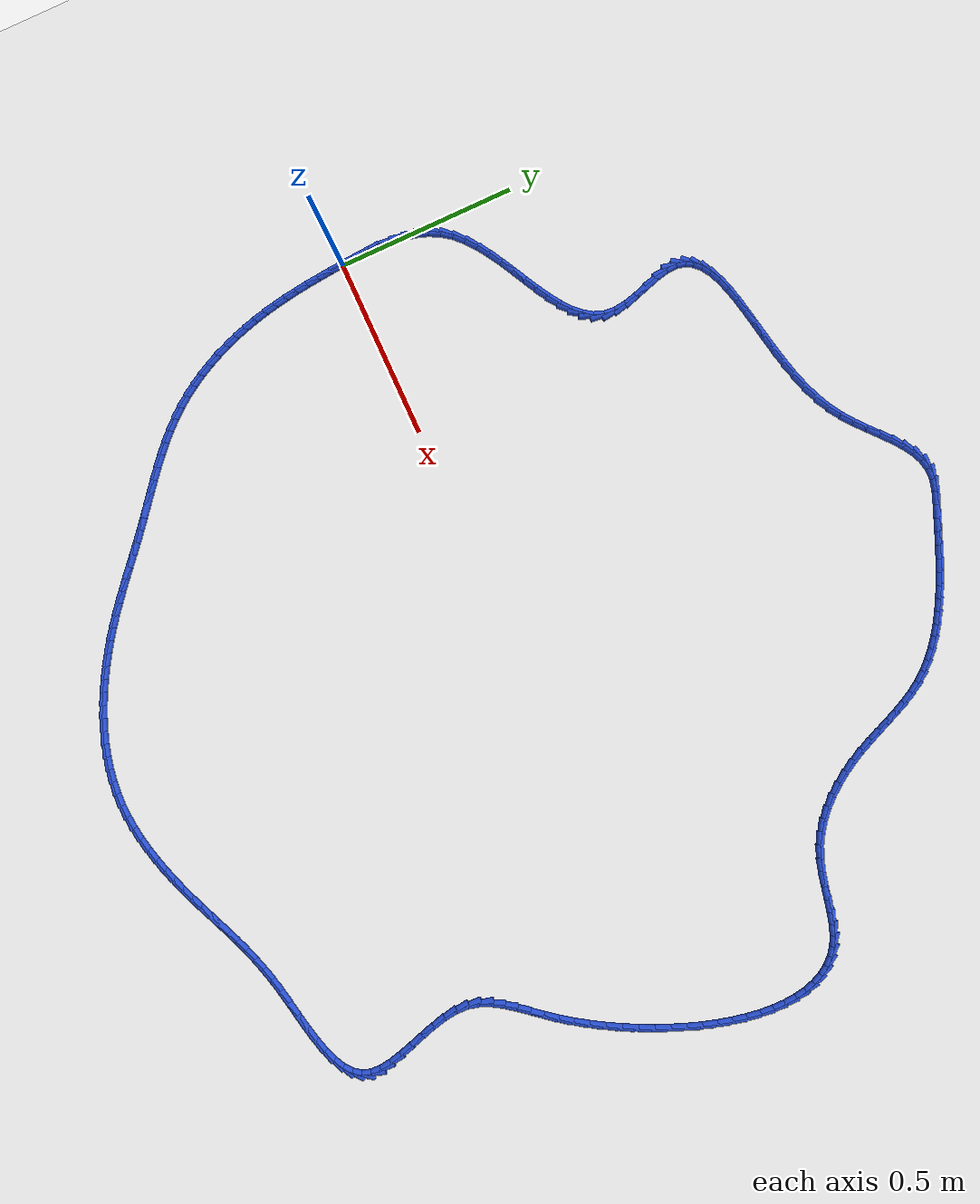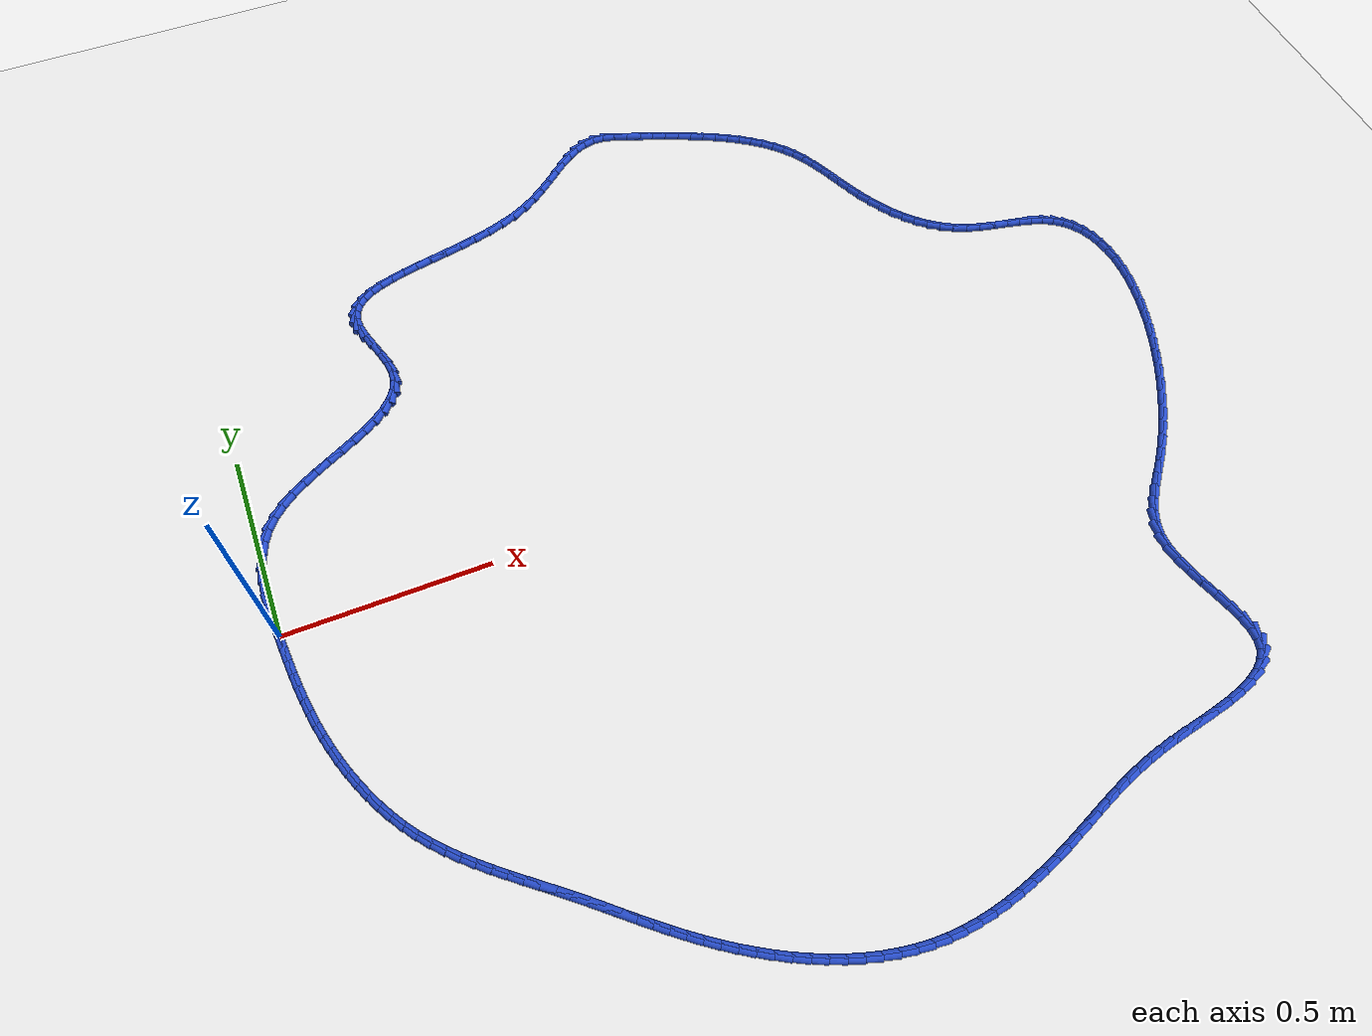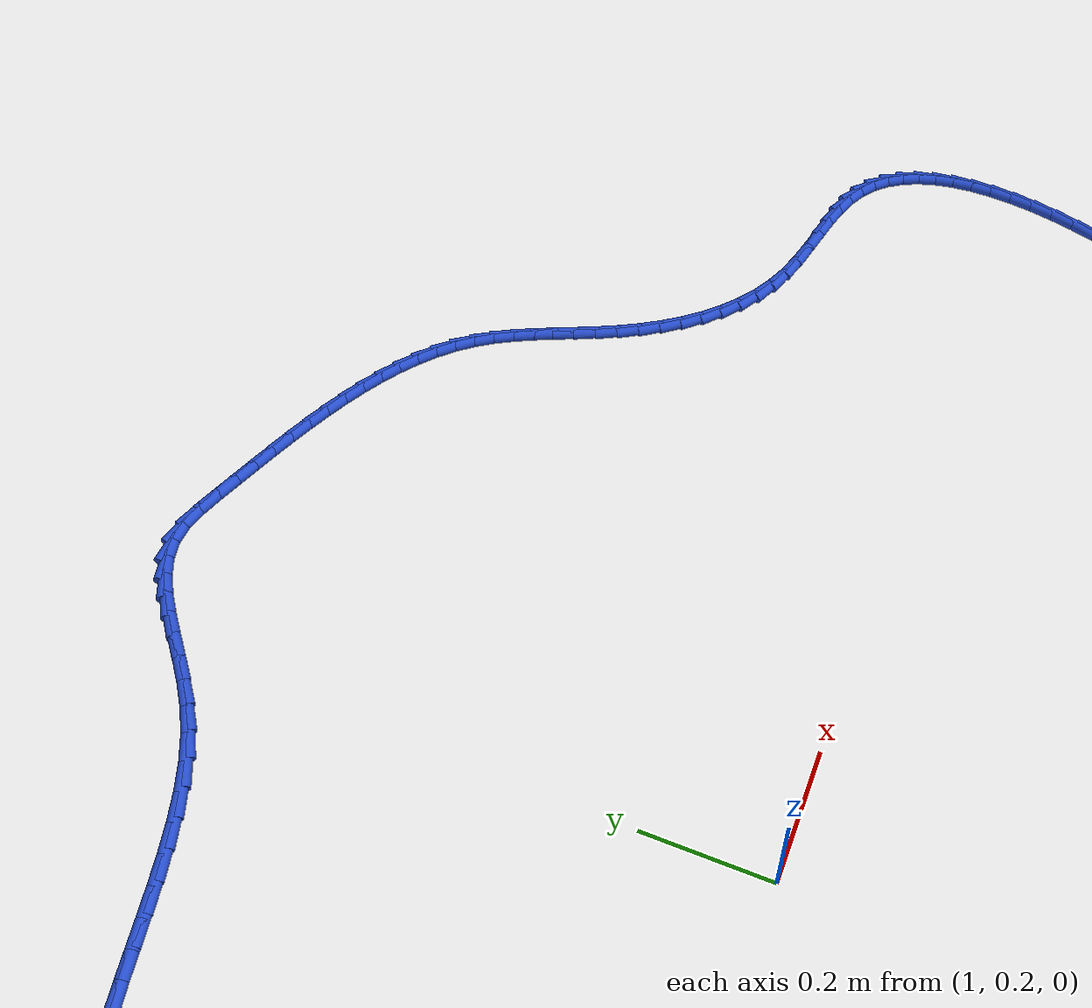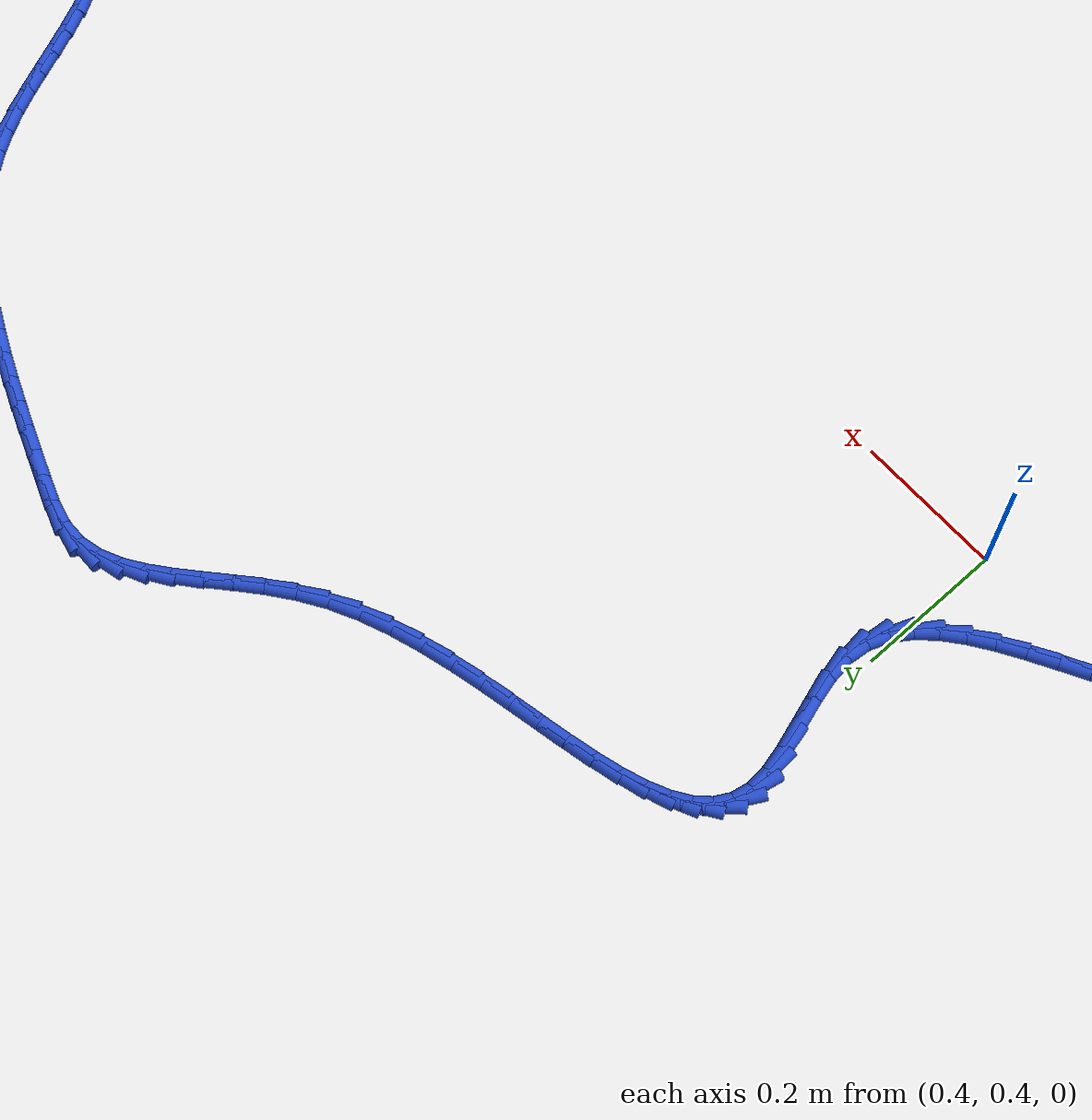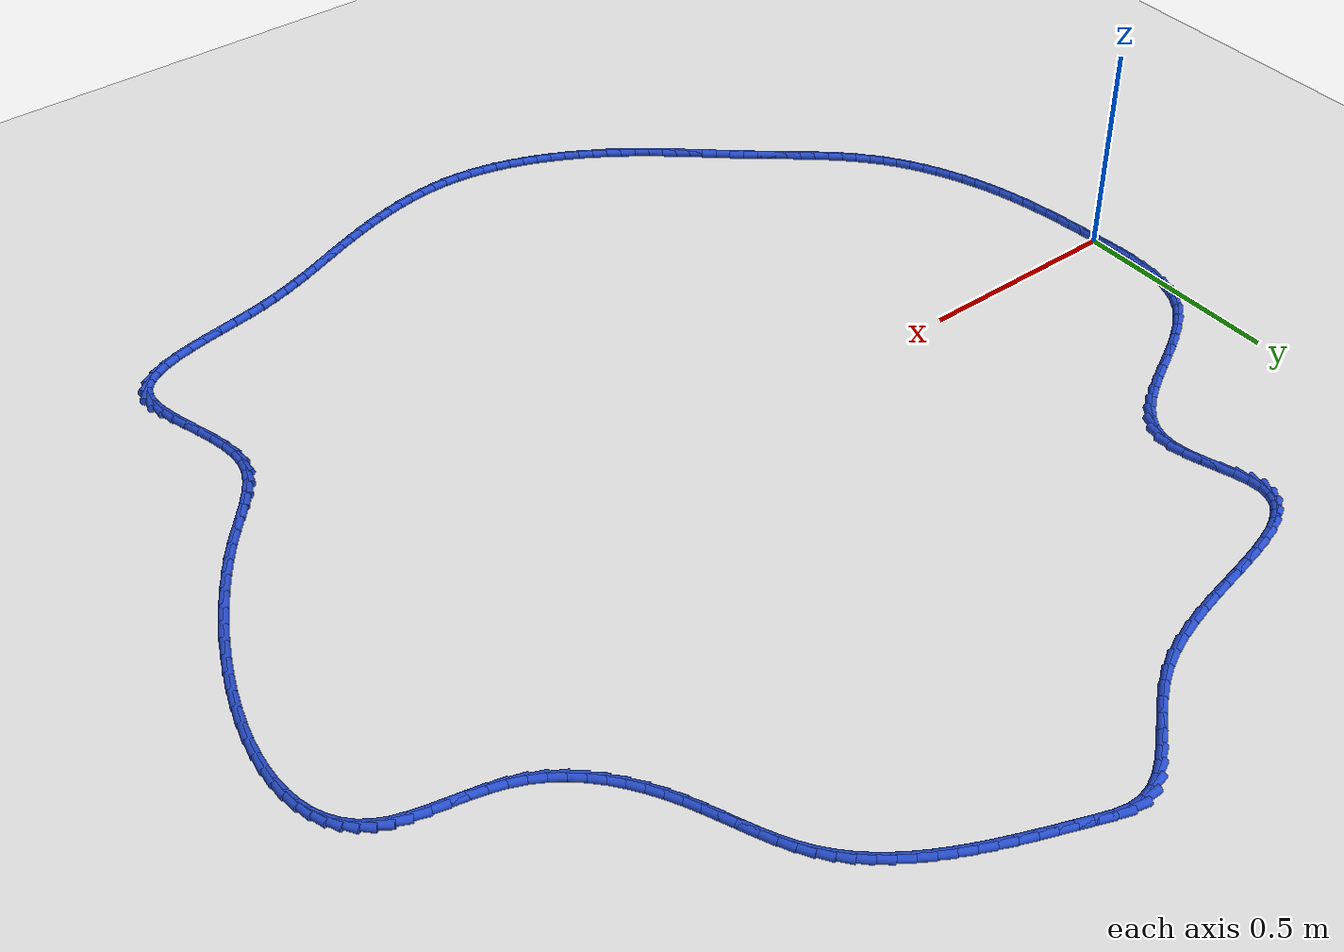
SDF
<sdf version="1.6">
 <world name="default">
  <light name="sun" type="directional">
   <pose>0 0 10 0 -0 0</pose>
   <diffuse>0.8 0.8 0.8 1</diffuse>
   <specular>0.2 0.2 0.2 1</specular>
   <attenuation>
    <range>1000</range>
    <constant>0.9</constant>
    <linear>0.01</linear>
    <quadratic>0.001</quadratic>
   </attenuation>
   <direction>-0.5 0.1 -0.9</direction>
  </light>
  <model name="ground_plane">
   <static>1</static>
   <link name="link">
    <collision name="collision">
     <geometry><plane><normal>0 0 1</normal><size>100 100</size></plane></geometry>
     <surface><friction><ode><mu>100</mu><mu2>50</mu2></ode></friction></surface>
    </collision>
    <visual name="visual">
     <cast_shadows>0</cast_shadows>
     <geometry><plane><normal>0 0 1</normal><size>100 100</size></plane></geometry>
     <material>
      <script><uri>file://media/materials/scripts/gazebo.material</uri><name>Gazebo/WhiteGlow</name></script>
     </material>
    </visual>
   </link>
  </model>
  <gravity>0 0 -9.8</gravity>
  <magnetic_field>6e-06 2.3e-05 -4.2e-05</magnetic_field>
  <atmosphere type="adiabatic"/>
  <physics name="default_physics" default="0" type="ode">
   <max_step_size>0.001</max_step_size>
   <real_time_factor>1</real_time_factor>
   <real_time_update_rate>1000</real_time_update_rate>
  </physics>
  <scene><ambient>0.4 0.4 0.4 1</ambient><background>0.7 0.7 0.7 1</background><shadows>1</shadows></scene>
  <spherical_coordinates>
   <surface_model>EARTH_WGS84</surface_model>
   <latitude_deg>0</latitude_deg>
   <longitude_deg>0</longitude_deg>
   <elevation>0</elevation>
   <heading_deg>0</heading_deg>
  </spherical_coordinates>
  <model name="line">
   <link name="link_0">
    <pose>-1.214306433183765e-17 3.469446951953614e-17 0.01 0 1.57 -1.4988204890219934</pose>
    <collision name="collision">
     <geometry><cylinder><radius>0.01</radius><length>0.08</length></cylinder></geometry>
    </collision>
    <visual name="visual">
     <material>
      <script><name>Gazebo/Blue</name><uri>file://media/materials/scripts/gazebo.material</uri></script>
     </material>
     <geometry><cylinder><radius>0.01</radius><length>0.08</length></cylinder></geometry>
    </visual>
   </link>
   <link name="link_1">
    <pose>-0.0026443736135458623 0.03667627506879169 0.01 0 1.57 -1.5200555862646792</pose>
    <collision name="collision">
     <geometry><cylinder><radius>0.01</radius><length>0.08</length></cylinder></geometry>
    </collision>
    <visual name="visual">
     <material>
      <script><name>Gazebo/Blue</name><uri>file://media/materials/scripts/gazebo.material</uri></script>
     </material>
     <geometry><cylinder><radius>0.01</radius><length>0.08</length></cylinder></geometry>
    </visual>
   </link>
   <link name="link_2">
    <pose>-0.004520874620253348 0.07362666805158882 0.01 0 1.57 -1.5569291936119904</pose>
    <collision name="collision">
     <geometry><cylinder><radius>0.01</radius><length>0.08</length></cylinder></geometry>
    </collision>
    <visual name="visual">
     <material>
      <script><name>Gazebo/Blue</name><uri>file://media/materials/scripts/gazebo.material</uri></script>
     </material>
     <geometry><cylinder><radius>0.01</radius><length>0.08</length></cylinder></geometry>
    </visual>
   </link>
   <link name="link_3">
    <pose>-0.0050316268119205325 0.11045615874308516 0.01 0 1.57 1.5308085638260238</pose>
    <collision name="collision">
     <geometry><cylinder><radius>0.01</radius><length>0.08</length></cylinder></geometry>
    </collision>
    <visual name="visual">
     <material>
      <script><name>Gazebo/Blue</name><uri>file://media/materials/scripts/gazebo.material</uri></script>
     </material>
     <geometry><cylinder><radius>0.01</radius><length>0.08</length></cylinder></geometry>
    </visual>
   </link>
   <link name="link_4">
    <pose>-0.003578753980345477 0.1467697269379744 0.01 0 1.57 1.4578866126188785</pose>
    <collision name="collision">
     <geometry><cylinder><radius>0.01</radius><length>0.08</length></cylinder></geometry>
    </collision>
    <visual name="visual">
     <material>
      <script><name>Gazebo/Blue</name><uri>file://media/materials/scripts/gazebo.material</uri></script>
     </material>
     <geometry><cylinder><radius>0.01</radius><length>0.08</length></cylinder></geometry>
    </visual>
   </link>
   <link name="link_5">
    <pose>0.00043562008267375267 0.18217235243095029 0.01 0 1.57 1.3634262907586991</pose>
    <collision name="collision">
     <geometry><cylinder><radius>0.01</radius><length>0.08</length></cylinder></geometry>
    </collision>
    <visual name="visual">
     <material>
      <script><name>Gazebo/Blue</name><uri>file://media/materials/scripts/gazebo.material</uri></script>
     </material>
     <geometry><cylinder><radius>0.01</radius><length>0.08</length></cylinder></geometry>
    </visual>
   </link>
   <link name="link_6">
    <pose>0.007609371585339093 0.21626901501670653 0.01 0 1.57 1.2453707688888733</pose>
    <collision name="collision">
     <geometry><cylinder><radius>0.01</radius><length>0.08</length></cylinder></geometry>
    </collision>
    <visual name="visual">
     <material>
      <script><name>Gazebo/Blue</name><uri>file://media/materials/scripts/gazebo.material</uri></script>
     </material>
     <geometry><cylinder><radius>0.01</radius><length>0.08</length></cylinder></geometry>
    </visual>
   </link>
   <link name="link_7">
    <pose>0.018540376735852494 0.2486646944899369 0.01 0 1.57 1.1035565594660215</pose>
    <collision name="collision">
     <geometry><cylinder><radius>0.01</radius><length>0.08</length></cylinder></geometry>
    </collision>
    <visual name="visual">
     <material>
      <script><name>Gazebo/Blue</name><uri>file://media/materials/scripts/gazebo.material</uri></script>
     </material>
     <geometry><cylinder><radius>0.01</radius><length>0.08</length></cylinder></geometry>
    </visual>
   </link>
   <link name="link_8">
    <pose>0.033826511742415855 0.27896437064533514 0.01 0 1.57 0.9423853496840386</pose>
    <collision name="collision">
     <geometry><cylinder><radius>0.01</radius><length>0.08</length></cylinder></geometry>
    </collision>
    <visual name="visual">
     <material>
      <script><name>Gazebo/Blue</name><uri>file://media/materials/scripts/gazebo.material</uri></script>
     </material>
     <geometry><cylinder><radius>0.01</radius><length>0.08</length></cylinder></geometry>
    </visual>
   </link>
   <link name="link_9">
    <pose>0.0540432695106379 0.3067849416293125 0.01 0 1.57 0.7909087358598685</pose>
    <collision name="collision">
     <geometry><cylinder><radius>0.01</radius><length>0.08</length></cylinder></geometry>
    </collision>
    <visual name="visual">
     <material>
      <script><name>Gazebo/Blue</name><uri>file://media/materials/scripts/gazebo.material</uri></script>
     </material>
     <geometry><cylinder><radius>0.01</radius><length>0.08</length></cylinder></geometry>
    </visual>
   </link>
   <link name="link_10">
    <pose>0.07908616511224484 0.3321053707907126 0.01 0 1.57 0.675497220498085</pose>
    <collision name="collision">
     <geometry><cylinder><radius>0.01</radius><length>0.08</length></cylinder></geometry>
    </collision>
    <visual name="visual">
     <material>
      <script><name>Gazebo/Blue</name><uri>file://media/materials/scripts/gazebo.material</uri></script>
     </material>
     <geometry><cylinder><radius>0.01</radius><length>0.08</length></cylinder></geometry>
    </visual>
   </link>
   <link name="link_11">
    <pose>0.10806393874775722 0.35532355249173947 0.01 0 1.57 0.5927258947456043</pose>
    <collision name="collision">
     <geometry><cylinder><radius>0.01</radius><length>0.08</length></cylinder></geometry>
    </collision>
    <visual name="visual">
     <material>
      <script><name>Gazebo/Blue</name><uri>file://media/materials/scripts/gazebo.material</uri></script>
     </material>
     <geometry><cylinder><radius>0.01</radius><length>0.08</length></cylinder></geometry>
    </visual>
   </link>
   <link name="link_12">
    <pose>0.1400414453115448 0.37686074853609786 0.01 0 1.57 0.5372213075551189</pose>
    <collision name="collision">
     <geometry><cylinder><radius>0.01</radius><length>0.08</length></cylinder></geometry>
    </collision>
    <visual name="visual">
     <material>
      <script><name>Gazebo/Blue</name><uri>file://media/materials/scripts/gazebo.material</uri></script>
     </material>
     <geometry><cylinder><radius>0.01</radius><length>0.08</length></cylinder></geometry>
    </visual>
   </link>
   <link name="link_13">
    <pose>0.17408353969797752 0.397138220727493 0.01 0 1.57 0.5049072847108641</pose>
    <collision name="collision">
     <geometry><cylinder><radius>0.01</radius><length>0.08</length></cylinder></geometry>
    </collision>
    <visual name="visual">
     <material>
      <script><name>Gazebo/Blue</name><uri>file://media/materials/scripts/gazebo.material</uri></script>
     </material>
     <geometry><cylinder><radius>0.01</radius><length>0.08</length></cylinder></geometry>
    </visual>
   </link>
   <link name="link_14">
    <pose>0.20925507680142524 0.41657723086963006 0.01 0 1.57 0.49347365034514207</pose>
    <collision name="collision">
     <geometry><cylinder><radius>0.01</radius><length>0.08</length></cylinder></geometry>
    </collision>
    <visual name="visual">
     <material>
      <script><name>Gazebo/Blue</name><uri>file://media/materials/scripts/gazebo.material</uri></script>
     </material>
     <geometry><cylinder><radius>0.01</radius><length>0.08</length></cylinder></geometry>
    </visual>
   </link>
   <link name="link_15">
    <pose>0.24462091151625764 0.43559904076621403 0.01 0 1.57 0.5024468519526988</pose>
    <collision name="collision">
     <geometry><cylinder><radius>0.01</radius><length>0.08</length></cylinder></geometry>
    </collision>
    <visual name="visual">
     <material>
      <script><name>Gazebo/Blue</name><uri>file://media/materials/scripts/gazebo.material</uri></script>
     </material>
     <geometry><cylinder><radius>0.01</radius><length>0.08</length></cylinder></geometry>
    </visual>
   </link>
   <link name="link_16">
    <pose>0.2792458987368447 0.45462491222095003 0.01 0 1.57 0.5332881999788075</pose>
    <collision name="collision">
     <geometry><cylinder><radius>0.01</radius><length>0.08</length></cylinder></geometry>
    </collision>
    <visual name="visual">
     <material>
      <script><name>Gazebo/Blue</name><uri>file://media/materials/scripts/gazebo.material</uri></script>
     </material>
     <geometry><cylinder><radius>0.01</radius><length>0.08</length></cylinder></geometry>
    </visual>
   </link>
   <link name="link_17">
    <pose>0.31219489335755607 0.474076107037543 0.01 0 1.57 0.589656181202302</pose>
    <collision name="collision">
     <geometry><cylinder><radius>0.01</radius><length>0.08</length></cylinder></geometry>
    </collision>
    <visual name="visual">
     <material>
      <script><name>Gazebo/Blue</name><uri>file://media/materials/scripts/gazebo.material</uri></script>
     </material>
     <geometry><cylinder><radius>0.01</radius><length>0.08</length></cylinder></geometry>
    </visual>
   </link>
   <link name="link_18">
    <pose>0.34253275027276175 0.49437388701969814 0.01 0 1.57 0.6777462787563344</pose>
    <collision name="collision">
     <geometry><cylinder><radius>0.01</radius><length>0.08</length></cylinder></geometry>
    </collision>
    <visual name="visual">
     <material>
      <script><name>Gazebo/Blue</name><uri>file://media/materials/scripts/gazebo.material</uri></script>
     </material>
     <geometry><cylinder><radius>0.01</radius><length>0.08</length></cylinder></geometry>
    </visual>
   </link>
   <link name="link_19">
    <pose>0.36932432437683166 0.5159395139711206 0.01 0 1.57 0.806125842627991</pose>
    <collision name="collision">
     <geometry><cylinder><radius>0.01</radius><length>0.08</length></cylinder></geometry>
    </collision>
    <visual name="visual">
     <material>
      <script><name>Gazebo/Blue</name><uri>file://media/materials/scripts/gazebo.material</uri></script>
     </material>
     <geometry><cylinder><radius>0.01</radius><length>0.08</length></cylinder></geometry>
    </visual>
   </link>
   <link name="link_20">
    <pose>0.39163447056413525 0.5391942496955151 0.01 0 1.57 0.9832441418283961</pose>
    <collision name="collision">
     <geometry><cylinder><radius>0.01</radius><length>0.08</length></cylinder></geometry>
    </collision>
    <visual name="visual">
     <material>
      <script><name>Gazebo/Blue</name><uri>file://media/materials/scripts/gazebo.material</uri></script>
     </material>
     <geometry><cylinder><radius>0.01</radius><length>0.08</length></cylinder></geometry>
    </visual>
   </link>
   <link name="link_21">
    <pose>0.4085280437290427 0.564559355996587 0.01 0 1.57 1.2094957342139134</pose>
    <collision name="collision">
     <geometry><cylinder><radius>0.01</radius><length>0.08</length></cylinder></geometry>
    </collision>
    <visual name="visual">
     <material>
      <script><name>Gazebo/Blue</name><uri>file://media/materials/scripts/gazebo.material</uri></script>
     </material>
     <geometry><cylinder><radius>0.01</radius><length>0.08</length></cylinder></geometry>
    </visual>
   </link>
   <link name="link_22">
    <pose>0.4190698987659235 0.5924560946780411 0.01 0 1.57 1.4655568719264143</pose>
    <collision name="collision">
     <geometry><cylinder><radius>0.01</radius><length>0.08</length></cylinder></geometry>
    </collision>
    <visual name="visual">
     <material>
      <script><name>Gazebo/Blue</name><uri>file://media/materials/scripts/gazebo.material</uri></script>
     </material>
     <geometry><cylinder><radius>0.01</radius><length>0.08</length></cylinder></geometry>
    </visual>
   </link>
   <link name="link_23">
    <pose>0.42232835905987604 0.6233040488498596 0.01 0 1.57 -1.453269252564613</pose>
    <collision name="collision">
     <geometry><cylinder><radius>0.01</radius><length>0.08</length></cylinder></geometry>
    </collision>
    <visual name="visual">
     <material>
      <script><name>Gazebo/Blue</name><uri>file://media/materials/scripts/gazebo.material</uri></script>
     </material>
     <geometry><cylinder><radius>0.01</radius><length>0.08</length></cylinder></geometry>
    </visual>
   </link>
   <link name="link_24">
    <pose>0.4183436487180534 0.6570524173049758 0.01 0 1.57 -1.3253362792650358</pose>
    <collision name="collision">
     <geometry><cylinder><radius>0.01</radius><length>0.08</length></cylinder></geometry>
    </collision>
    <visual name="visual">
     <material>
      <script><name>Gazebo/Blue</name><uri>file://media/materials/scripts/gazebo.material</uri></script>
     </material>
     <geometry><cylinder><radius>0.01</radius><length>0.08</length></cylinder></geometry>
    </visual>
   </link>
   <link name="link_25">
    <pose>0.4094540579785947 0.6925381717919168 0.01 0 1.57 -1.2703103494876535</pose>
    <collision name="collision">
     <geometry><cylinder><radius>0.01</radius><length>0.08</length></cylinder></geometry>
    </collision>
    <visual name="visual">
     <material>
      <script><name>Gazebo/Blue</name><uri>file://media/materials/scripts/gazebo.material</uri></script>
     </material>
     <geometry><cylinder><radius>0.01</radius><length>0.08</length></cylinder></geometry>
    </visual>
   </link>
   <link name="link_26">
    <pose>0.39832995634646606 0.7284375630353555 0.01 0 1.57 -1.2743269905875352</pose>
    <collision name="collision">
     <geometry><cylinder><radius>0.01</radius><length>0.08</length></cylinder></geometry>
    </collision>
    <visual name="visual">
     <material>
      <script><name>Gazebo/Blue</name><uri>file://media/materials/scripts/gazebo.material</uri></script>
     </material>
     <geometry><cylinder><radius>0.01</radius><length>0.08</length></cylinder></geometry>
    </visual>
   </link>
   <link name="link_27">
    <pose>0.38764171332663366 0.7634268417599653 0.01 0 1.57 -1.3433288088316944</pose>
    <collision name="collision">
     <geometry><cylinder><radius>0.01</radius><length>0.08</length></cylinder></geometry>
    </collision>
    <visual name="visual">
     <material>
      <script><name>Gazebo/Blue</name><uri>file://media/materials/scripts/gazebo.material</uri></script>
     </material>
     <geometry><cylinder><radius>0.01</radius><length>0.08</length></cylinder></geometry>
    </visual>
   </link>
   <link name="link_28">
    <pose>0.38005969842406373 0.7961822586904197 0.01 0 1.57 -1.508160542037202</pose>
    <collision name="collision">
     <geometry><cylinder><radius>0.01</radius><length>0.08</length></cylinder></geometry>
    </collision>
    <visual name="visual">
     <material>
      <script><name>Gazebo/Blue</name><uri>file://media/materials/scripts/gazebo.material</uri></script>
     </material>
     <geometry><cylinder><radius>0.01</radius><length>0.08</length></cylinder></geometry>
    </visual>
   </link>
   <link name="link_29">
    <pose>0.378227563490017 0.8253946066307822 0.01 0 1.57 1.3636173697189506</pose>
    <collision name="collision">
     <geometry><cylinder><radius>0.01</radius><length>0.08</length></cylinder></geometry>
    </collision>
    <visual name="visual">
     <material>
      <script><name>Gazebo/Blue</name><uri>file://media/materials/scripts/gazebo.material</uri></script>
     </material>
     <geometry><cylinder><radius>0.01</radius><length>0.08</length></cylinder></geometry>
    </visual>
   </link>
   <link name="link_30">
    <pose>0.38349586716752904 0.8504584925860481 0.01 0 1.57 1.0624609753797698</pose>
    <collision name="collision">
     <geometry><cylinder><radius>0.01</radius><length>0.08</length></cylinder></geometry>
    </collision>
    <visual name="visual">
     <material>
      <script><name>Gazebo/Blue</name><uri>file://media/materials/scripts/gazebo.material</uri></script>
     </material>
     <geometry><cylinder><radius>0.01</radius><length>0.08</length></cylinder></geometry>
    </visual>
   </link>
   <link name="link_31">
    <pose>0.39537129361239426 0.8717721210131194 0.01 0 1.57 0.7907053357896994</pose>
    <collision name="collision">
     <geometry><cylinder><radius>0.01</radius><length>0.08</length></cylinder></geometry>
    </collision>
    <visual name="visual">
     <material>
      <script><name>Gazebo/Blue</name><uri>file://media/materials/scripts/gazebo.material</uri></script>
     </material>
     <geometry><cylinder><radius>0.01</radius><length>0.08</length></cylinder></geometry>
    </visual>
   </link>
   <link name="link_32">
    <pose>0.4132192868463547 0.8898105715790193 0.01 0 1.57 0.5814354681504732</pose>
    <collision name="collision">
     <geometry><cylinder><radius>0.01</radius><length>0.08</length></cylinder></geometry>
    </collision>
    <visual name="visual">
     <material>
      <script><name>Gazebo/Blue</name><uri>file://media/materials/scripts/gazebo.material</uri></script>
     </material>
     <geometry><cylinder><radius>0.01</radius><length>0.08</length></cylinder></geometry>
    </visual>
   </link>
   <link name="link_33">
    <pose>0.4364052908911517 0.9050489239507703 0.01 0 1.57 0.4336271711486278</pose>
    <collision name="collision">
     <geometry><cylinder><radius>0.01</radius><length>0.08</length></cylinder></geometry>
    </collision>
    <visual name="visual">
     <material>
      <script><name>Gazebo/Blue</name><uri>file://media/materials/scripts/gazebo.material</uri></script>
     </material>
     <geometry><cylinder><radius>0.01</radius><length>0.08</length></cylinder></geometry>
    </visual>
   </link>
   <link name="link_34">
    <pose>0.46429474976852714 0.917962257795396 0.01 0 1.57 0.33326907307639436</pose>
    <collision name="collision">
     <geometry><cylinder><radius>0.01</radius><length>0.08</length></cylinder></geometry>
    </collision>
    <visual name="visual">
     <material>
      <script><name>Gazebo/Blue</name><uri>file://media/materials/scripts/gazebo.material</uri></script>
     </material>
     <geometry><cylinder><radius>0.01</radius><length>0.08</length></cylinder></geometry>
    </visual>
   </link>
   <link name="link_35">
    <pose>0.49625310750022267 0.9290256527799192 0.01 0 1.57 0.2671980473761101</pose>
    <collision name="collision">
     <geometry><cylinder><radius>0.01</radius><length>0.08</length></cylinder></geometry>
    </collision>
    <visual name="visual">
     <material>
      <script><name>Gazebo/Blue</name><uri>file://media/materials/scripts/gazebo.material</uri></script>
     </material>
     <geometry><cylinder><radius>0.01</radius><length>0.08</length></cylinder></geometry>
    </visual>
   </link>
   <link name="link_36">
    <pose>0.5316458081079795 0.9387141885713629 0.01 0 1.57 0.22617989518240167</pose>
    <collision name="collision">
     <geometry><cylinder><radius>0.01</radius><length>0.08</length></cylinder></geometry>
    </collision>
    <visual name="visual">
     <material>
      <script><name>Gazebo/Blue</name><uri>file://media/materials/scripts/gazebo.material</uri></script>
     </material>
     <geometry><cylinder><radius>0.01</radius><length>0.08</length></cylinder></geometry>
    </visual>
   </link>
   <link name="link_37">
    <pose>0.5698382956135398 0.94750294483675 0.01 0 1.57 0.20435497722791757</pose>
    <collision name="collision">
     <geometry><cylinder><radius>0.01</radius><length>0.08</length></cylinder></geometry>
    </collision>
    <visual name="visual">
     <material>
      <script><name>Gazebo/Blue</name><uri>file://media/materials/scripts/gazebo.material</uri></script>
     </material>
     <geometry><cylinder><radius>0.01</radius><length>0.08</length></cylinder></geometry>
    </visual>
   </link>
   <link name="link_38">
    <pose>0.6101960140386451 0.9558670012431036 0.01 0 1.57 0.1982391782111296</pose>
    <collision name="collision">
     <geometry><cylinder><radius>0.01</radius><length>0.08</length></cylinder></geometry>
    </collision>
    <visual name="visual">
     <material>
      <script><name>Gazebo/Blue</name><uri>file://media/materials/scripts/gazebo.material</uri></script>
     </material>
     <geometry><cylinder><radius>0.01</radius><length>0.08</length></cylinder></geometry>
    </visual>
   </link>
   <link name="link_39">
    <pose>0.6520844074050368 0.9642814374574471 0.01 0 1.57 0.20598794016074992</pose>
    <collision name="collision">
     <geometry><cylinder><radius>0.01</radius><length>0.08</length></cylinder></geometry>
    </collision>
    <visual name="visual">
     <material>
      <script><name>Gazebo/Blue</name><uri>file://media/materials/scripts/gazebo.material</uri></script>
     </material>
     <geometry><cylinder><radius>0.01</radius><length>0.08</length></cylinder></geometry>
    </visual>
   </link>
   <link name="link_40">
    <pose>0.6948689197344569 0.9732213331468029 0.01 0 1.57 0.22694717492236063</pose>
    <collision name="collision">
     <geometry><cylinder><radius>0.01</radius><length>0.08</length></cylinder></geometry>
    </collision>
    <visual name="visual">
     <material>
      <script><name>Gazebo/Blue</name><uri>file://media/materials/scripts/gazebo.material</uri></script>
     </material>
     <geometry><cylinder><radius>0.01</radius><length>0.08</length></cylinder></geometry>
    </visual>
   </link>
   <link name="link_41">
    <pose>0.7379149950486468 0.9831617679781944 0.01 0 1.57 0.26140219757968153</pose>
    <collision name="collision">
     <geometry><cylinder><radius>0.01</radius><length>0.08</length></cylinder></geometry>
    </collision>
    <visual name="visual">
     <material>
      <script><name>Gazebo/Blue</name><uri>file://media/materials/scripts/gazebo.material</uri></script>
     </material>
     <geometry><cylinder><radius>0.01</radius><length>0.08</length></cylinder></geometry>
    </visual>
   </link>
   <link name="link_42">
    <pose>0.780588077369348 0.9945778216186446 0.01 0 1.57 0.3104382364628737</pose>
    <collision name="collision">
     <geometry><cylinder><radius>0.01</radius><length>0.08</length></cylinder></geometry>
    </collision>
    <visual name="visual">
     <material>
      <script><name>Gazebo/Blue</name><uri>file://media/materials/scripts/gazebo.material</uri></script>
     </material>
     <geometry><cylinder><radius>0.01</radius><length>0.08</length></cylinder></geometry>
    </visual>
   </link>
   <link name="link_43">
    <pose>0.8222536107183026 1.0079445737351762 0.01 0 1.57 0.37582710529346797</pose>
    <collision name="collision">
     <geometry><cylinder><radius>0.01</radius><length>0.08</length></cylinder></geometry>
    </collision>
    <visual name="visual">
     <material>
      <script><name>Gazebo/Blue</name><uri>file://media/materials/scripts/gazebo.material</uri></script>
     </material>
     <geometry><cylinder><radius>0.01</radius><length>0.08</length></cylinder></geometry>
    </visual>
   </link>
   <link name="link_44">
    <pose>0.8622770391172518 1.0237371039948127 0.01 0 1.57 0.4598255329981359</pose>
    <collision name="collision">
     <geometry><cylinder><radius>0.01</radius><length>0.08</length></cylinder></geometry>
    </collision>
    <visual name="visual">
     <material>
      <script><name>Gazebo/Blue</name><uri>file://media/materials/scripts/gazebo.material</uri></script>
     </material>
     <geometry><cylinder><radius>0.01</radius><length>0.08</length></cylinder></geometry>
    </visual>
   </link>
   <link name="link_45">
    <pose>0.9000238065879372 1.0424304920645766 0.01 0 1.57 0.5593611234795564</pose>
    <collision name="collision">
     <geometry><cylinder><radius>0.01</radius><length>0.08</length></cylinder></geometry>
    </collision>
    <visual name="visual">
     <material>
      <script><name>Gazebo/Blue</name><uri>file://media/materials/scripts/gazebo.material</uri></script>
     </material>
     <geometry><cylinder><radius>0.01</radius><length>0.08</length></cylinder></geometry>
    </visual>
   </link>
   <link name="link_46">
    <pose>0.9349840197975766 1.0643176794510192 0.01 0 1.57 0.6427878481176166</pose>
    <collision name="collision">
     <geometry><cylinder><radius>0.01</radius><length>0.08</length></cylinder></geometry>
    </collision>
    <visual name="visual">
     <material>
      <script><name>Gazebo/Blue</name><uri>file://media/materials/scripts/gazebo.material</uri></script>
     </material>
     <geometry><cylinder><radius>0.01</radius><length>0.08</length></cylinder></geometry>
    </visual>
   </link>
   <link name="link_47">
    <pose>0.9673995603719717 1.0885932280496735 0.01 0 1.57 0.6970854625959797</pose>
    <collision name="collision">
     <geometry><cylinder><radius>0.01</radius><length>0.08</length></cylinder></geometry>
    </collision>
    <visual name="visual">
     <material>
      <script><name>Gazebo/Blue</name><uri>file://media/materials/scripts/gazebo.material</uri></script>
     </material>
     <geometry><cylinder><radius>0.01</radius><length>0.08</length></cylinder></geometry>
    </visual>
   </link>
   <link name="link_48">
    <pose>0.9977927330122429 1.114041988066598 0.01 0 1.57 0.7212600121073419</pose>
    <collision name="collision">
     <geometry><cylinder><radius>0.01</radius><length>0.08</length></cylinder></geometry>
    </collision>
    <visual name="visual">
     <material>
      <script><name>Gazebo/Blue</name><uri>file://media/materials/scripts/gazebo.material</uri></script>
     </material>
     <geometry><cylinder><radius>0.01</radius><length>0.08</length></cylinder></geometry>
    </visual>
   </link>
   <link name="link_49">
    <pose>1.0266863213653643 1.1394481099447684 0.01 0 1.57 0.7131302030304955</pose>
    <collision name="collision">
     <geometry><cylinder><radius>0.01</radius><length>0.08</length></cylinder></geometry>
    </collision>
    <visual name="visual">
     <material>
      <script><name>Gazebo/Blue</name><uri>file://media/materials/scripts/gazebo.material</uri></script>
     </material>
     <geometry><cylinder><radius>0.01</radius><length>0.08</length></cylinder></geometry>
    </visual>
   </link>
   <link name="link_50">
    <pose>1.0546031090783108 1.1635957441271612 0.01 0 1.57 0.6681135769106458</pose>
    <collision name="collision">
     <geometry><cylinder><radius>0.01</radius><length>0.08</length></cylinder></geometry>
    </collision>
    <visual name="visual">
     <material>
      <script><name>Gazebo/Blue</name><uri>file://media/materials/scripts/gazebo.material</uri></script>
     </material>
     <geometry><cylinder><radius>0.01</radius><length>0.08</length></cylinder></geometry>
    </visual>
   </link>
   <link name="link_51">
    <pose>1.0820658797980576 1.1852690410567528 0.01 0 1.57 0.5786090154069308</pose>
    <collision name="collision">
     <geometry><cylinder><radius>0.01</radius><length>0.08</length></cylinder></geometry>
    </collision>
    <visual name="visual">
     <material>
      <script><name>Gazebo/Blue</name><uri>file://media/materials/scripts/gazebo.material</uri></script>
     </material>
     <geometry><cylinder><radius>0.01</radius><length>0.08</length></cylinder></geometry>
    </visual>
   </link>
   <link name="link_52">
    <pose>1.1095974171715786 1.203252151176519 0.01 0 1.57 0.4352529361032434</pose>
    <collision name="collision">
     <geometry><cylinder><radius>0.01</radius><length>0.08</length></cylinder></geometry>
    </collision>
    <visual name="visual">
     <material>
      <script><name>Gazebo/Blue</name><uri>file://media/materials/scripts/gazebo.material</uri></script>
     </material>
     <geometry><cylinder><radius>0.01</radius><length>0.08</length></cylinder></geometry>
    </visual>
   </link>
   <link name="link_53">
    <pose>1.1377205048458492 1.2163292249294364 0.01 0 1.57 0.23354562962634384</pose>
    <collision name="collision">
     <geometry><cylinder><radius>0.01</radius><length>0.08</length></cylinder></geometry>
    </collision>
    <visual name="visual">
     <material>
      <script><name>Gazebo/Blue</name><uri>file://media/materials/scripts/gazebo.material</uri></script>
     </material>
     <geometry><cylinder><radius>0.01</radius><length>0.08</length></cylinder></geometry>
    </visual>
   </link>
   <link name="link_54">
    <pose>1.1669579264678434 1.2232844127584808 0.01 0 1.57 -0.012354326176410944</pose>
    <collision name="collision">
     <geometry><cylinder><radius>0.01</radius><length>0.08</length></cylinder></geometry>
    </collision>
    <visual name="visual">
     <material>
      <script><name>Gazebo/Blue</name><uri>file://media/materials/scripts/gazebo.material</uri></script>
     </material>
     <geometry><cylinder><radius>0.01</radius><length>0.08</length></cylinder></geometry>
    </visual>
   </link>
   <link name="link_55">
    <pose>1.1978321677283736 1.2229029629044839 0.01 0 1.57 -0.23482022662056876</pose>
    <collision name="collision">
     <geometry><cylinder><radius>0.01</radius><length>0.08</length></cylinder></geometry>
    </collision>
    <visual name="visual">
     <material>
      <script><name>Gazebo/Blue</name><uri>file://media/materials/scripts/gazebo.material</uri></script>
     </material>
     <geometry><cylinder><radius>0.01</radius><length>0.08</length></cylinder></geometry>
    </visual>
   </link>
   <link name="link_56">
    <pose>1.2305667169351786 1.2150717577655303 0.01 0 1.57 -0.34549519572329923</pose>
    <collision name="collision">
     <geometry><cylinder><radius>0.01</radius><length>0.08</length></cylinder></geometry>
    </collision>
    <visual name="visual">
     <material>
      <script><name>Gazebo/Blue</name><uri>file://media/materials/scripts/gazebo.material</uri></script>
     </material>
     <geometry><cylinder><radius>0.01</radius><length>0.08</length></cylinder></geometry>
    </visual>
   </link>
   <link name="link_57">
    <pose>1.2645242254718843 1.20284937090862 0.01 0 1.57 -0.36834525169890103</pose>
    <collision name="collision">
     <geometry><cylinder><radius>0.01</radius><length>0.08</length></cylinder></geometry>
    </collision>
    <visual name="visual">
     <material>
      <script><name>Gazebo/Blue</name><uri>file://media/materials/scripts/gazebo.material</uri></script>
     </material>
     <geometry><cylinder><radius>0.01</radius><length>0.08</length></cylinder></geometry>
    </visual>
   </link>
   <link name="link_58">
    <pose>1.2989614365680435 1.1895579609489573 0.01 0 1.57 -0.369934051005723</pose>
    <collision name="collision">
     <geometry><cylinder><radius>0.01</radius><length>0.08</length></cylinder></geometry>
    </collision>
    <visual name="visual">
     <material>
      <script><name>Gazebo/Blue</name><uri>file://media/materials/scripts/gazebo.material</uri></script>
     </material>
     <geometry><cylinder><radius>0.01</radius><length>0.08</length></cylinder></geometry>
    </visual>
   </link>
   <link name="link_59">
    <pose>1.333508387578357 1.1761610923221923 0.01 0 1.57 -0.3769370977065394</pose>
    <collision name="collision">
     <geometry><cylinder><radius>0.01</radius><length>0.08</length></cylinder></geometry>
    </collision>
    <visual name="visual">
     <material>
      <script><name>Gazebo/Blue</name><uri>file://media/materials/scripts/gazebo.material</uri></script>
     </material>
     <geometry><cylinder><radius>0.01</radius><length>0.08</length></cylinder></geometry>
    </visual>
   </link>
   <link name="link_60">
    <pose>1.3679697342631993 1.1625190333563753 0.01 0 1.57 -0.38957011054085855</pose>
    <collision name="collision">
     <geometry><cylinder><radius>0.01</radius><length>0.08</length></cylinder></geometry>
    </collision>
    <visual name="visual">
     <material>
      <script><name>Gazebo/Blue</name><uri>file://media/materials/scripts/gazebo.material</uri></script>
     </material>
     <geometry><cylinder><radius>0.01</radius><length>0.08</length></cylinder></geometry>
    </visual>
   </link>
   <link name="link_61">
    <pose>1.402151125338897 1.1484857785595965 0.01 0 1.57 -0.4080096239372377</pose>
    <collision name="collision">
     <geometry><cylinder><radius>0.01</radius><length>0.08</length></cylinder></geometry>
    </collision>
    <visual name="visual">
     <material>
      <script><name>Gazebo/Blue</name><uri>file://media/materials/scripts/gazebo.material</uri></script>
     </material>
     <geometry><cylinder><radius>0.01</radius><length>0.08</length></cylinder></geometry>
    </visual>
   </link>
   <link name="link_62">
    <pose>1.4358582095217785 1.1339153224399448 0.01 0 1.57 -0.4325364883144789</pose>
    <collision name="collision">
     <geometry><cylinder><radius>0.01</radius><length>0.08</length></cylinder></geometry>
    </collision>
    <visual name="visual">
     <material>
      <script><name>Gazebo/Blue</name><uri>file://media/materials/scripts/gazebo.material</uri></script>
     </material>
     <geometry><cylinder><radius>0.01</radius><length>0.08</length></cylinder></geometry>
    </visual>
   </link>
   <link name="link_63">
    <pose>1.4688966355281714 1.118661659505509 0.01 0 1.57 -0.46352743470910035</pose>
    <collision name="collision">
     <geometry><cylinder><radius>0.01</radius><length>0.08</length></cylinder></geometry>
    </collision>
    <visual name="visual">
     <material>
      <script><name>Gazebo/Blue</name><uri>file://media/materials/scripts/gazebo.material</uri></script>
     </material>
     <geometry><cylinder><radius>0.01</radius><length>0.08</length></cylinder></geometry>
    </visual>
   </link>
   <link name="link_64">
    <pose>1.5010720520744034 1.1025787842643804 0.01 0 1.57 -0.5014398132862841</pose>
    <collision name="collision">
     <geometry><cylinder><radius>0.01</radius><length>0.08</length></cylinder></geometry>
    </collision>
    <visual name="visual">
     <material>
      <script><name>Gazebo/Blue</name><uri>file://media/materials/scripts/gazebo.material</uri></script>
     </material>
     <geometry><cylinder><radius>0.01</radius><length>0.08</length></cylinder></geometry>
    </visual>
   </link>
   <link name="link_65">
    <pose>1.5321901078768023 1.085520691224647 0.01 0 1.57 -0.5467840213888382</pose>
    <collision name="collision">
     <geometry><cylinder><radius>0.01</radius><length>0.08</length></cylinder></geometry>
    </collision>
    <visual name="visual">
     <material>
      <script><name>Gazebo/Blue</name><uri>file://media/materials/scripts/gazebo.material</uri></script>
     </material>
     <geometry><cylinder><radius>0.01</radius><length>0.08</length></cylinder></geometry>
    </visual>
   </link>
   <link name="link_66">
    <pose>1.5620564516516964 1.0673413748943985 0.01 0 1.57 -0.6000763377242626</pose>
    <collision name="collision">
     <geometry><cylinder><radius>0.01</radius><length>0.08</length></cylinder></geometry>
    </collision>
    <visual name="visual">
     <material>
      <script><name>Gazebo/Blue</name><uri>file://media/materials/scripts/gazebo.material</uri></script>
     </material>
     <geometry><cylinder><radius>0.01</radius><length>0.08</length></cylinder></geometry>
    </visual>
   </link>
   <link name="link_67">
    <pose>1.5904767321154125 1.0478948297817245 0.01 0 1.57 -0.6617639091767967</pose>
    <collision name="collision">
     <geometry><cylinder><radius>0.01</radius><length>0.08</length></cylinder></geometry>
    </collision>
    <visual name="visual">
     <material>
      <script><name>Gazebo/Blue</name><uri>file://media/materials/scripts/gazebo.material</uri></script>
     </material>
     <geometry><cylinder><radius>0.01</radius><length>0.08</length></cylinder></geometry>
    </visual>
   </link>
   <link name="link_68">
    <pose>1.6172565979842786 1.027035050394715 0.01 0 1.57 -0.7321154279929465</pose>
    <collision name="collision">
     <geometry><cylinder><radius>0.01</radius><length>0.08</length></cylinder></geometry>
    </collision>
    <visual name="visual">
     <material>
      <script><name>Gazebo/Blue</name><uri>file://media/materials/scripts/gazebo.material</uri></script>
     </material>
     <geometry><cylinder><radius>0.01</radius><length>0.08</length></cylinder></geometry>
    </visual>
   </link>
   <link name="link_69">
    <pose>1.642201697974623 1.0046160312414587 0.01 0 1.57 -0.8110786397383414</pose>
    <collision name="collision">
     <geometry><cylinder><radius>0.01</radius><length>0.08</length></cylinder></geometry>
    </collision>
    <visual name="visual">
     <material>
      <script><name>Gazebo/Blue</name><uri>file://media/materials/scripts/gazebo.material</uri></script>
     </material>
     <geometry><cylinder><radius>0.01</radius><length>0.08</length></cylinder></geometry>
    </visual>
   </link>
   <link name="link_70">
    <pose>1.6651176808027737 0.9804917668300461 0.01 0 1.57 -0.8981221280467298</pose>
    <collision name="collision">
     <geometry><cylinder><radius>0.01</radius><length>0.08</length></cylinder></geometry>
    </collision>
    <visual name="visual">
     <material>
      <script><name>Gazebo/Blue</name><uri>file://media/materials/scripts/gazebo.material</uri></script>
     </material>
     <geometry><cylinder><radius>0.01</radius><length>0.08</length></cylinder></geometry>
    </visual>
   </link>
   <link name="link_71">
    <pose>1.6858101951850573 0.9545162516685659 0.01 0 1.57 -0.9898430854239947</pose>
    <collision name="collision">
     <geometry><cylinder><radius>0.01</radius><length>0.08</length></cylinder></geometry>
    </collision>
    <visual name="visual">
     <material>
      <script><name>Gazebo/Blue</name><uri>file://media/materials/scripts/gazebo.material</uri></script>
     </material>
     <geometry><cylinder><radius>0.01</radius><length>0.08</length></cylinder></geometry>
    </visual>
   </link>
   <link name="link_72">
    <pose>1.7041473118764539 0.9265859685996188 0.01 0 1.57 -1.06720877741418</pose>
    <collision name="collision">
     <geometry><cylinder><radius>0.01</radius><length>0.08</length></cylinder></geometry>
    </collision>
    <visual name="visual">
     <material>
      <script><name>Gazebo/Blue</name><uri>file://media/materials/scripts/gazebo.material</uri></script>
     </material>
     <geometry><cylinder><radius>0.01</radius><length>0.08</length></cylinder></geometry>
    </visual>
   </link>
   <link name="link_73">
    <pose>1.7204865536937664 0.8969305520798676 0.01 0 1.57 -1.1218937048782442</pose>
    <collision name="collision">
     <geometry><cylinder><radius>0.01</radius><length>0.08</length></cylinder></geometry>
    </collision>
    <visual name="visual">
     <material>
      <script><name>Gazebo/Blue</name><uri>file://media/materials/scripts/gazebo.material</uri></script>
     </material>
     <geometry><cylinder><radius>0.01</radius><length>0.08</length></cylinder></geometry>
    </visual>
   </link>
   <link name="link_74">
    <pose>1.7354163226657566 0.8659367873640151 0.01 0 1.57 -1.1548604417931472</pose>
    <collision name="collision">
     <geometry><cylinder><radius>0.01</radius><length>0.08</length></cylinder></geometry>
    </collision>
    <visual name="visual">
     <material>
      <script><name>Gazebo/Blue</name><uri>file://media/materials/scripts/gazebo.material</uri></script>
     </material>
     <geometry><cylinder><radius>0.01</radius><length>0.08</length></cylinder></geometry>
    </visual>
   </link>
   <link name="link_75">
    <pose>1.7495263804599803 0.8339923851617661 0.01 0 1.57 -1.1672464423177176</pose>
    <collision name="collision">
     <geometry><cylinder><radius>0.01</radius><length>0.08</length></cylinder></geometry>
    </collision>
    <visual name="visual">
     <material>
      <script><name>Gazebo/Blue</name><uri>file://media/materials/scripts/gazebo.material</uri></script>
     </material>
     <geometry><cylinder><radius>0.01</radius><length>0.08</length></cylinder></geometry>
    </visual>
   </link>
   <link name="link_76">
    <pose>1.763406488743996 0.8014850561828258 0.01 0 1.57 -1.1598942168717836</pose>
    <collision name="collision">
     <geometry><cylinder><radius>0.01</radius><length>0.08</length></cylinder></geometry>
    </collision>
    <visual name="visual">
     <material>
      <script><name>Gazebo/Blue</name><uri>file://media/materials/scripts/gazebo.material</uri></script>
     </material>
     <geometry><cylinder><radius>0.01</radius><length>0.08</length></cylinder></geometry>
    </visual>
   </link>
   <link name="link_77">
    <pose>1.7776464091853594 0.7688025111368998 0.01 0 1.57 -1.1332387958826544</pose>
    <collision name="collision">
     <geometry><cylinder><radius>0.01</radius><length>0.08</length></cylinder></geometry>
    </collision>
    <visual name="visual">
     <material>
      <script><name>Gazebo/Blue</name><uri>file://media/materials/scripts/gazebo.material</uri></script>
     </material>
     <geometry><cylinder><radius>0.01</radius><length>0.08</length></cylinder></geometry>
    </visual>
   </link>
   <link name="link_78">
    <pose>1.792835903451629 0.7363324607336933 0.01 0 1.57 -1.0879475176500455</pose>
    <collision name="collision">
     <geometry><cylinder><radius>0.01</radius><length>0.08</length></cylinder></geometry>
    </collision>
    <visual name="visual">
     <material>
      <script><name>Gazebo/Blue</name><uri>file://media/materials/scripts/gazebo.material</uri></script>
     </material>
     <geometry><cylinder><radius>0.01</radius><length>0.08</length></cylinder></geometry>
    </visual>
   </link>
   <link name="link_79">
    <pose>1.809543944156576 0.7044613122296399 0.01 0 1.57 -1.0313115824833643</pose>
    <collision name="collision">
     <geometry><cylinder><radius>0.01</radius><length>0.08</length></cylinder></geometry>
    </collision>
    <visual name="visual">
     <material>
      <script><name>Gazebo/Blue</name><uri>file://media/materials/scripts/gazebo.material</uri></script>
     </material>
     <geometry><cylinder><radius>0.01</radius><length>0.08</length></cylinder></geometry>
    </visual>
   </link>
   <link name="link_80">
    <pose>1.8280471793707649 0.6735571444191857 0.01 0 1.57 -0.9680225889423671</pose>
    <collision name="collision">
     <geometry><cylinder><radius>0.01</radius><length>0.08</length></cylinder></geometry>
    </collision>
    <visual name="visual">
     <material>
      <script><name>Gazebo/Blue</name><uri>file://media/materials/scripts/gazebo.material</uri></script>
     </material>
     <geometry><cylinder><radius>0.01</radius><length>0.08</length></cylinder></geometry>
    </visual>
   </link>
   <link name="link_81">
    <pose>1.8484064409963321 0.643974504634804 0.01 0 1.57 -0.8972457717322905</pose>
    <collision name="collision">
     <geometry><cylinder><radius>0.01</radius><length>0.08</length></cylinder></geometry>
    </collision>
    <visual name="visual">
     <material>
      <script><name>Gazebo/Blue</name><uri>file://media/materials/scripts/gazebo.material</uri></script>
     </material>
     <geometry><cylinder><radius>0.01</radius><length>0.08</length></cylinder></geometry>
    </visual>
   </link>
   <link name="link_82">
    <pose>1.8706775165778693 0.6160676239327012 0.01 0 1.57 -0.8180752421338745</pose>
    <collision name="collision">
     <geometry><cylinder><radius>0.01</radius><length>0.08</length></cylinder></geometry>
    </collision>
    <visual name="visual">
     <material>
      <script><name>Gazebo/Blue</name><uri>file://media/materials/scripts/gazebo.material</uri></script>
     </material>
     <geometry><cylinder><radius>0.01</radius><length>0.08</length></cylinder></geometry>
    </visual>
   </link>
   <link name="link_83">
    <pose>1.8949161936599652 0.5901907333690837 0.01 0 1.57 -0.729794570306116</pose>
    <collision name="collision">
     <geometry><cylinder><radius>0.01</radius><length>0.08</length></cylinder></geometry>
    </collision>
    <visual name="visual">
     <material>
      <script><name>Gazebo/Blue</name><uri>file://media/materials/scripts/gazebo.material</uri></script>
     </material>
     <geometry><cylinder><radius>0.01</radius><length>0.08</length></cylinder></geometry>
    </visual>
   </link>
   <link name="link_84">
    <pose>1.9211782597872125 0.5666980640001578 0.01 0 1.57 -0.632074817677574</pose>
    <collision name="collision">
     <geometry><cylinder><radius>0.01</radius><length>0.08</length></cylinder></geometry>
    </collision>
    <visual name="visual">
     <material>
      <script><name>Gazebo/Blue</name><uri>file://media/materials/scripts/gazebo.material</uri></script>
     </material>
     <geometry><cylinder><radius>0.01</radius><length>0.08</length></cylinder></geometry>
    </visual>
   </link>
   <link name="link_85">
    <pose>1.9495195025042003 0.545943846882129 0.01 0 1.57 -0.5252236216582464</pose>
    <collision name="collision">
     <geometry><cylinder><radius>0.01</radius><length>0.08</length></cylinder></geometry>
    </collision>
    <visual name="visual">
     <material>
      <script><name>Gazebo/Blue</name><uri>file://media/materials/scripts/gazebo.material</uri></script>
     </material>
     <geometry><cylinder><radius>0.01</radius><length>0.08</length></cylinder></geometry>
    </visual>
   </link>
   <link name="link_86">
    <pose>1.9799957093555192 0.5282823130712044 0.01 0 1.57 -0.4107193899825467</pose>
    <collision name="collision">
     <geometry><cylinder><radius>0.01</radius><length>0.08</length></cylinder></geometry>
    </collision>
    <visual name="visual">
     <material>
      <script><name>Gazebo/Blue</name><uri>file://media/materials/scripts/gazebo.material</uri></script>
     </material>
     <geometry><cylinder><radius>0.01</radius><length>0.08</length></cylinder></geometry>
    </visual>
   </link>
   <link name="link_87">
    <pose>2.012656753294385 0.5140588609305979 0.01 0 1.57 -0.30753480163709424</pose>
    <collision name="collision">
     <geometry><cylinder><radius>0.01</radius><length>0.08</length></cylinder></geometry>
    </collision>
    <visual name="visual">
     <material>
      <script><name>Gazebo/Blue</name><uri>file://media/materials/scripts/gazebo.material</uri></script>
     </material>
     <geometry><cylinder><radius>0.01</radius><length>0.08</length></cylinder></geometry>
    </visual>
   </link>
   <link name="link_88">
    <pose>2.0471972749186067 0.5030883942996339 0.01 0 1.57 -0.24058591781186892</pose>
    <collision name="collision">
     <geometry><cylinder><radius>0.01</radius><length>0.08</length></cylinder></geometry>
    </collision>
    <visual name="visual">
     <material>
      <script><name>Gazebo/Blue</name><uri>file://media/materials/scripts/gazebo.material</uri></script>
     </material>
     <geometry><cylinder><radius>0.01</radius><length>0.08</length></cylinder></geometry>
    </visual>
   </link>
   <link name="link_89">
    <pose>2.0827610993751464 0.49436324391610675 0.01 0 1.57 -0.20872957087108948</pose>
    <collision name="collision">
     <geometry><cylinder><radius>0.01</radius><length>0.08</length></cylinder></geometry>
    </collision>
    <visual name="visual">
     <material>
      <script><name>Gazebo/Blue</name><uri>file://media/materials/scripts/gazebo.material</uri></script>
     </material>
     <geometry><cylinder><radius>0.01</radius><length>0.08</length></cylinder></geometry>
    </visual>
   </link>
   <link name="link_90">
    <pose>2.1184446458337205 0.4868049456959236 0.01 0 1.57 -0.2108578740167117</pose>
    <collision name="collision">
     <geometry><cylinder><radius>0.01</radius><length>0.08</length></cylinder></geometry>
    </collision>
    <visual name="visual">
     <material>
      <script><name>Gazebo/Blue</name><uri>file://media/materials/scripts/gazebo.material</uri></script>
     </material>
     <geometry><cylinder><radius>0.01</radius><length>0.08</length></cylinder></geometry>
    </visual>
   </link>
   <link name="link_91">
    <pose>2.153344333464042 0.4793350355549919 0.01 0 1.57 -0.24942064899093436</pose>
    <collision name="collision">
     <geometry><cylinder><radius>0.01</radius><length>0.08</length></cylinder></geometry>
    </collision>
    <visual name="visual">
     <material>
      <script><name>Gazebo/Blue</name><uri>file://media/materials/scripts/gazebo.material</uri></script>
     </material>
     <geometry><cylinder><radius>0.01</radius><length>0.08</length></cylinder></geometry>
    </visual>
   </link>
   <link name="link_92">
    <pose>2.186556581435828 0.4708750494092193 0.01 0 1.57 -0.33116848493613216</pose>
    <collision name="collision">
     <geometry><cylinder><radius>0.01</radius><length>0.08</length></cylinder></geometry>
    </collision>
    <visual name="visual">
     <material>
      <script><name>Gazebo/Blue</name><uri>file://media/materials/scripts/gazebo.material</uri></script>
     </material>
     <geometry><cylinder><radius>0.01</radius><length>0.08</length></cylinder></geometry>
    </visual>
   </link>
   <link name="link_93">
    <pose>2.2171778089187906 0.4603465231745131 0.01 0 1.57 -0.46635270470213464</pose>
    <collision name="collision">
     <geometry><cylinder><radius>0.01</radius><length>0.08</length></cylinder></geometry>
    </collision>
    <visual name="visual">
     <material>
      <script><name>Gazebo/Blue</name><uri>file://media/materials/scripts/gazebo.material</uri></script>
     </material>
     <geometry><cylinder><radius>0.01</radius><length>0.08</length></cylinder></geometry>
    </visual>
   </link>
   <link name="link_94">
    <pose>2.244315935691733 0.44668557124266 0.01 0 1.57 -0.6406188574766067</pose>
    <collision name="collision">
     <geometry><cylinder><radius>0.01</radius><length>0.08</length></cylinder></geometry>
    </collision>
    <visual name="visual">
     <material>
      <script><name>Gazebo/Blue</name><uri>file://media/materials/scripts/gazebo.material</uri></script>
     </material>
     <geometry><cylinder><radius>0.01</radius><length>0.08</length></cylinder></geometry>
    </visual>
   </link>
   <link name="link_95">
    <pose>2.267519660418898 0.42938705096431534 0.01 0 1.57 -0.8186222880513925</pose>
    <collision name="collision">
     <geometry><cylinder><radius>0.01</radius><length>0.08</length></cylinder></geometry>
    </collision>
    <visual name="visual">
     <material>
      <script><name>Gazebo/Blue</name><uri>file://media/materials/scripts/gazebo.material</uri></script>
     </material>
     <geometry><cylinder><radius>0.01</radius><length>0.08</length></cylinder></geometry>
    </visual>
   </link>
   <link name="link_96">
    <pose>2.2869066467481503 0.4086670547332448 0.01 0 1.57 -0.9884060970715556</pose>
    <collision name="collision">
     <geometry><cylinder><radius>0.01</radius><length>0.08</length></cylinder></geometry>
    </collision>
    <visual name="visual">
     <material>
      <script><name>Gazebo/Blue</name><uri>file://media/materials/scripts/gazebo.material</uri></script>
     </material>
     <geometry><cylinder><radius>0.01</radius><length>0.08</length></cylinder></geometry>
    </visual>
   </link>
   <link name="link_97">
    <pose>2.3026322210118106 0.38478941715692455 0.01 0 1.57 -1.1426019666059637</pose>
    <collision name="collision">
     <geometry><cylinder><radius>0.01</radius><length>0.08</length></cylinder></geometry>
    </collision>
    <visual name="visual">
     <material>
      <script><name>Gazebo/Blue</name><uri>file://media/materials/scripts/gazebo.material</uri></script>
     </material>
     <geometry><cylinder><radius>0.01</radius><length>0.08</length></cylinder></geometry>
    </visual>
   </link>
   <link name="link_98">
    <pose>2.3148517095421908 0.35801797284283043 0.01 0 1.57 -1.277832947994499</pose>
    <collision name="collision">
     <geometry><cylinder><radius>0.01</radius><length>0.08</length></cylinder></geometry>
    </collision>
    <visual name="visual">
     <material>
      <script><name>Gazebo/Blue</name><uri>file://media/materials/scripts/gazebo.material</uri></script>
     </material>
     <geometry><cylinder><radius>0.01</radius><length>0.08</length></cylinder></geometry>
    </visual>
   </link>
   <link name="link_99">
    <pose>2.3237204386716104 0.3286165563984396 0.01 0 1.57 -1.394071651430606</pose>
    <collision name="collision">
     <geometry><cylinder><radius>0.01</radius><length>0.08</length></cylinder></geometry>
    </collision>
    <visual name="visual">
     <material>
      <script><name>Gazebo/Blue</name><uri>file://media/materials/scripts/gazebo.material</uri></script>
     </material>
     <geometry><cylinder><radius>0.01</radius><length>0.08</length></cylinder></geometry>
    </visual>
   </link>
   <link name="link_100">
    <pose>2.3293937347323856 0.2968490024312282 0.01 0 1.57 -1.4932080649780168</pose>
    <collision name="collision">
     <geometry><cylinder><radius>0.01</radius><length>0.08</length></cylinder></geometry>
    </collision>
    <visual name="visual">
     <material>
      <script><name>Gazebo/Blue</name><uri>file://media/materials/scripts/gazebo.material</uri></script>
     </material>
     <geometry><cylinder><radius>0.01</radius><length>0.08</length></cylinder></geometry>
    </visual>
   </link>
   <link name="link_101">
    <pose>2.3320269240568328 0.26297914554867197 0.01 0 1.57 1.5637507172580294</pose>
    <collision name="collision">
     <geometry><cylinder><radius>0.01</radius><length>0.08</length></cylinder></geometry>
    </collision>
    <visual name="visual">
     <material>
      <script><name>Gazebo/Blue</name><uri>file://media/materials/scripts/gazebo.material</uri></script>
     </material>
     <geometry><cylinder><radius>0.01</radius><length>0.08</length></cylinder></geometry>
    </visual>
   </link>
   <link name="link_102">
    <pose>2.3317753329772666 0.22727082035824808 0.01 0 1.57 1.4910087584285268</pose>
    <collision name="collision">
     <geometry><cylinder><radius>0.01</radius><length>0.08</length></cylinder></geometry>
    </collision>
    <visual name="visual">
     <material>
      <script><name>Gazebo/Blue</name><uri>file://media/materials/scripts/gazebo.material</uri></script>
     </material>
     <geometry><cylinder><radius>0.01</radius><length>0.08</length></cylinder></geometry>
    </visual>
   </link>
   <link name="link_103">
    <pose>2.3287942878260064 0.18998786146743263 0.01 0 1.57 1.4278385541445826</pose>
    <collision name="collision">
     <geometry><cylinder><radius>0.01</radius><length>0.08</length></cylinder></geometry>
    </collision>
    <visual name="visual">
     <material>
      <script><name>Gazebo/Blue</name><uri>file://media/materials/scripts/gazebo.material</uri></script>
     </material>
     <geometry><cylinder><radius>0.01</radius><length>0.08</length></cylinder></geometry>
    </visual>
   </link>
   <link name="link_104">
    <pose>2.323239114935366 0.15139410348370183 0.01 0 1.57 1.3722893516417625</pose>
    <collision name="collision">
     <geometry><cylinder><radius>0.01</radius><length>0.08</length></cylinder></geometry>
    </collision>
    <visual name="visual">
     <material>
      <script><name>Gazebo/Blue</name><uri>file://media/materials/scripts/gazebo.material</uri></script>
     </material>
     <geometry><cylinder><radius>0.01</radius><length>0.08</length></cylinder></geometry>
    </visual>
   </link>
   <link name="link_105">
    <pose>2.315265140637665 0.11175338101453211 0.01 0 1.57 1.3227586585079127</pose>
    <collision name="collision">
     <geometry><cylinder><radius>0.01</radius><length>0.08</length></cylinder></geometry>
    </collision>
    <visual name="visual">
     <material>
      <script><name>Gazebo/Blue</name><uri>file://media/materials/scripts/gazebo.material</uri></script>
     </material>
     <geometry><cylinder><radius>0.01</radius><length>0.08</length></cylinder></geometry>
    </visual>
   </link>
   <link name="link_106">
    <pose>2.3050276912652174 0.07132952866739888 0.01 0 1.57 1.2779362122470375</pose>
    <collision name="collision">
     <geometry><cylinder><radius>0.01</radius><length>0.08</length></cylinder></geometry>
    </collision>
    <visual name="visual">
     <material>
      <script><name>Gazebo/Blue</name><uri>file://media/materials/scripts/gazebo.material</uri></script>
     </material>
     <geometry><cylinder><radius>0.01</radius><length>0.08</length></cylinder></geometry>
    </visual>
   </link>
   <link name="link_107">
    <pose>2.29268209315034 0.03038638104978026 0.01 0 1.57 1.2367423751138578</pose>
    <collision name="collision">
     <geometry><cylinder><radius>0.01</radius><length>0.08</length></cylinder></geometry>
    </collision>
    <visual name="visual">
     <material>
      <script><name>Gazebo/Blue</name><uri>file://media/materials/scripts/gazebo.material</uri></script>
     </material>
     <geometry><cylinder><radius>0.01</radius><length>0.08</length></cylinder></geometry>
    </visual>
   </link>
   <link name="link_108">
    <pose>2.27838367262535 -0.01081222723084823 0.01 0 1.57 1.1982718985527017</pose>
    <collision name="collision">
     <geometry><cylinder><radius>0.01</radius><length>0.08</length></cylinder></geometry>
    </collision>
    <visual name="visual">
     <material>
      <script><name>Gazebo/Blue</name><uri>file://media/materials/scripts/gazebo.material</uri></script>
     </material>
     <geometry><cylinder><radius>0.01</radius><length>0.08</length></cylinder></geometry>
    </visual>
   </link>
   <link name="link_109">
    <pose>2.262287756022564 -0.05200246156701027 0.01 0 1.57 1.1617456749066437</pose>
    <collision name="collision">
     <geometry><cylinder><radius>0.01</radius><length>0.08</length></cylinder></geometry>
    </collision>
    <visual name="visual">
     <material>
      <script><name>Gazebo/Blue</name><uri>file://media/materials/scripts/gazebo.material</uri></script>
     </material>
     <geometry><cylinder><radius>0.01</radius><length>0.08</length></cylinder></geometry>
    </visual>
   </link>
   <link name="link_110">
    <pose>2.2445496696742984 -0.09292048735122954 0.01 0 1.57 1.1264696901405122</pose>
    <collision name="collision">
     <geometry><cylinder><radius>0.01</radius><length>0.08</length></cylinder></geometry>
    </collision>
    <visual name="visual">
     <material>
      <script><name>Gazebo/Blue</name><uri>file://media/materials/scripts/gazebo.material</uri></script>
     </material>
     <geometry><cylinder><radius>0.01</radius><length>0.08</length></cylinder></geometry>
    </visual>
   </link>
   <link name="link_111">
    <pose>2.225324739912869 -0.13330246997602968 0.01 0 1.57 1.0917991537720473</pose>
    <collision name="collision">
     <geometry><cylinder><radius>0.01</radius><length>0.08</length></cylinder></geometry>
    </collision>
    <visual name="visual">
     <material>
      <script><name>Gazebo/Blue</name><uri>file://media/materials/scripts/gazebo.material</uri></script>
     </material>
     <geometry><cylinder><radius>0.01</radius><length>0.08</length></cylinder></geometry>
    </visual>
   </link>
   <link name="link_112">
    <pose>2.2047682930705923 -0.1728845748339352 0.01 0 1.57 1.0571053711042913</pose>
    <collision name="collision">
     <geometry><cylinder><radius>0.01</radius><length>0.08</length></cylinder></geometry>
    </collision>
    <visual name="visual">
     <material>
      <script><name>Gazebo/Blue</name><uri>file://media/materials/scripts/gazebo.material</uri></script>
     </material>
     <geometry><cylinder><radius>0.01</radius><length>0.08</length></cylinder></geometry>
    </visual>
   </link>
   <link name="link_113">
    <pose>2.1830356554797867 -0.211402967317468 0.01 0 1.57 1.0217427125383582</pose>
    <collision name="collision">
     <geometry><cylinder><radius>0.01</radius><length>0.08</length></cylinder></geometry>
    </collision>
    <visual name="visual">
     <material>
      <script><name>Gazebo/Blue</name><uri>file://media/materials/scripts/gazebo.material</uri></script>
     </material>
     <geometry><cylinder><radius>0.01</radius><length>0.08</length></cylinder></geometry>
    </visual>
   </link>
   <link name="link_114">
    <pose>2.1602821534727665 -0.2485938128191526 0.01 0 1.57 0.9850127236353062</pose>
    <collision name="collision">
     <geometry><cylinder><radius>0.01</radius><length>0.08</length></cylinder></geometry>
    </collision>
    <visual name="visual">
     <material>
      <script><name>Gazebo/Blue</name><uri>file://media/materials/scripts/gazebo.material</uri></script>
     </material>
     <geometry><cylinder><radius>0.01</radius><length>0.08</length></cylinder></geometry>
    </visual>
   </link>
   <link name="link_115">
    <pose>2.1366631133818488 -0.2841932767315126 0.01 0 1.57 0.9461218374191389</pose>
    <collision name="collision">
     <geometry><cylinder><radius>0.01</radius><length>0.08</length></cylinder></geometry>
    </collision>
    <visual name="visual">
     <material>
      <script><name>Gazebo/Blue</name><uri>file://media/materials/scripts/gazebo.material</uri></script>
     </material>
     <geometry><cylinder><radius>0.01</radius><length>0.08</length></cylinder></geometry>
    </visual>
   </link>
   <link name="link_116">
    <pose>2.112333861539352 -0.3179375244470719 0.01 0 1.57 0.9052762561392744</pose>
    <collision name="collision">
     <geometry><cylinder><radius>0.01</radius><length>0.08</length></cylinder></geometry>
    </collision>
    <visual name="visual">
     <material>
      <script><name>Gazebo/Blue</name><uri>file://media/materials/scripts/gazebo.material</uri></script>
     </material>
     <geometry><cylinder><radius>0.01</radius><length>0.08</length></cylinder></geometry>
    </visual>
   </link>
   <link name="link_117">
    <pose>2.087482012926452 -0.3495964109121663 0.01 0 1.57 0.8799756129789351</pose>
    <collision name="collision">
     <geometry><cylinder><radius>0.01</radius><length>0.08</length></cylinder></geometry>
    </collision>
    <visual name="visual">
     <material>
      <script><name>Gazebo/Blue</name><uri>file://media/materials/scripts/gazebo.material</uri></script>
     </material>
     <geometry><cylinder><radius>0.01</radius><length>0.08</length></cylinder></geometry>
    </visual>
   </link>
   <link name="link_118">
    <pose>2.062793503171662 -0.3794597323173659 0.01 0 1.57 0.8869054651624824</pose>
    <collision name="collision">
     <geometry><cylinder><radius>0.01</radius><length>0.08</length></cylinder></geometry>
    </collision>
    <visual name="visual">
     <material>
      <script><name>Gazebo/Blue</name><uri>file://media/materials/scripts/gazebo.material</uri></script>
     </material>
     <geometry><cylinder><radius>0.01</radius><length>0.08</length></cylinder></geometry>
    </visual>
   </link>
   <link name="link_119">
    <pose>2.0393457948378733 -0.4082257989344909 0.01 0 1.57 0.9310196389352378</pose>
    <collision name="collision">
     <geometry><cylinder><radius>0.01</radius><length>0.08</length></cylinder></geometry>
    </collision>
    <visual name="visual">
     <material>
      <script><name>Gazebo/Blue</name><uri>file://media/materials/scripts/gazebo.material</uri></script>
     </material>
     <geometry><cylinder><radius>0.01</radius><length>0.08</length></cylinder></geometry>
    </visual>
   </link>
   <link name="link_120">
    <pose>2.0182268901462126 -0.43660391797687775 0.01 0 1.57 1.0181088111532972</pose>
    <collision name="collision">
     <geometry><cylinder><radius>0.01</radius><length>0.08</length></cylinder></geometry>
    </collision>
    <visual name="visual">
     <material>
      <script><name>Gazebo/Blue</name><uri>file://media/materials/scripts/gazebo.material</uri></script>
     </material>
     <geometry><cylinder><radius>0.01</radius><length>0.08</length></cylinder></geometry>
    </visual>
   </link>
   <link name="link_121">
    <pose>2.000524791317805 -0.4653033966578646 0.01 0 1.57 1.1530245044313265</pose>
    <collision name="collision">
     <geometry><cylinder><radius>0.01</radius><length>0.08</length></cylinder></geometry>
    </collision>
    <visual name="visual">
     <material>
      <script><name>Gazebo/Blue</name><uri>file://media/materials/scripts/gazebo.material</uri></script>
     </material>
     <geometry><cylinder><radius>0.01</radius><length>0.08</length></cylinder></geometry>
    </visual>
   </link>
   <link name="link_122">
    <pose>1.987327500573776 -0.49503354219078877 0.01 0 1.57 1.3337000203145293</pose>
    <collision name="collision">
     <geometry><cylinder><radius>0.01</radius><length>0.08</length></cylinder></geometry>
    </collision>
    <visual name="visual">
     <material>
      <script><name>Gazebo/Blue</name><uri>file://media/materials/scripts/gazebo.material</uri></script>
     </material>
     <geometry><cylinder><radius>0.01</radius><length>0.08</length></cylinder></geometry>
    </visual>
   </link>
   <link name="link_123">
    <pose>1.9797230201352516 -0.526503661788988 0.01 0 1.57 1.536568834570541</pose>
    <collision name="collision">
     <geometry><cylinder><radius>0.01</radius><length>0.08</length></cylinder></geometry>
    </collision>
    <visual name="visual">
     <material>
      <script><name>Gazebo/Blue</name><uri>file://media/materials/scripts/gazebo.material</uri></script>
     </material>
     <geometry><cylinder><radius>0.01</radius><length>0.08</length></cylinder></geometry>
    </visual>
   </link>
   <link name="link_124">
    <pose>1.9785658915221223 -0.5602974525622767 0.01 0 1.57 -1.447188002186964</pose>
    <collision name="collision">
     <geometry><cylinder><radius>0.01</radius><length>0.08</length></cylinder></geometry>
    </collision>
    <visual name="visual">
     <material>
      <script><name>Gazebo/Blue</name><uri>file://media/materials/scripts/gazebo.material</uri></script>
     </material>
     <geometry><cylinder><radius>0.01</radius><length>0.08</length></cylinder></geometry>
    </visual>
   </link>
   <link name="link_125">
    <pose>1.9830121693577076 -0.5960847656764535 0.01 0 1.57 -1.3464169324519997</pose>
    <collision name="collision">
     <geometry><cylinder><radius>0.01</radius><length>0.08</length></cylinder></geometry>
    </collision>
    <visual name="visual">
     <material>
      <script><name>Gazebo/Blue</name><uri>file://media/materials/scripts/gazebo.material</uri></script>
     </material>
     <geometry><cylinder><radius>0.01</radius><length>0.08</length></cylinder></geometry>
    </visual>
   </link>
   <link name="link_126">
    <pose>1.9914670543561093 -0.6331314663726231 0.01 0 1.57 -1.2892751125752362</pose>
    <collision name="collision">
     <geometry><cylinder><radius>0.01</radius><length>0.08</length></cylinder></geometry>
    </collision>
    <visual name="visual">
     <material>
      <script><name>Gazebo/Blue</name><uri>file://media/materials/scripts/gazebo.material</uri></script>
     </material>
     <geometry><cylinder><radius>0.01</radius><length>0.08</length></cylinder></geometry>
    </visual>
   </link>
   <link name="link_127">
    <pose>2.002332422981825 -0.6707016313281876 0.01 0 1.57 -1.267827433095337</pose>
    <collision name="collision">
     <geometry><cylinder><radius>0.01</radius><length>0.08</length></cylinder></geometry>
    </collision>
    <visual name="visual">
     <material>
      <script><name>Gazebo/Blue</name><uri>file://media/materials/scripts/gazebo.material</uri></script>
     </material>
     <geometry><cylinder><radius>0.01</radius><length>0.08</length></cylinder></geometry>
    </visual>
   </link>
   <link name="link_128">
    <pose>2.014010151699355 -0.7080593372205487 0.01 0 1.57 -1.2801166031504412</pose>
    <collision name="collision">
     <geometry><cylinder><radius>0.01</radius><length>0.08</length></cylinder></geometry>
    </collision>
    <visual name="visual">
     <material>
      <script><name>Gazebo/Blue</name><uri>file://media/materials/scripts/gazebo.material</uri></script>
     </material>
     <geometry><cylinder><radius>0.01</radius><length>0.08</length></cylinder></geometry>
    </visual>
   </link>
   <link name="link_129">
    <pose>2.024902116973196 -0.7444686607271077 0.01 0 1.57 -1.330516857865101</pose>
    <collision name="collision">
     <geometry><cylinder><radius>0.01</radius><length>0.08</length></cylinder></geometry>
    </collision>
    <visual name="visual">
     <material>
      <script><name>Gazebo/Blue</name><uri>file://media/materials/scripts/gazebo.material</uri></script>
     </material>
     <geometry><cylinder><radius>0.01</radius><length>0.08</length></cylinder></geometry>
    </visual>
   </link>
   <link name="link_130">
    <pose>2.0334101952678494 -0.7791936785252662 0.01 0 1.57 -1.431597242822577</pose>
    <collision name="collision">
     <geometry><cylinder><radius>0.01</radius><length>0.08</length></cylinder></geometry>
    </collision>
    <visual name="visual">
     <material>
      <script><name>Gazebo/Blue</name><uri>file://media/materials/scripts/gazebo.material</uri></script>
     </material>
     <geometry><cylinder><radius>0.01</radius><length>0.08</length></cylinder></geometry>
    </visual>
   </link>
   <link name="link_131">
    <pose>2.0379362630478104 -0.8114984672924256 0.01 0 1.57 1.5346503075699747</pose>
    <collision name="collision">
     <geometry><cylinder><radius>0.01</radius><length>0.08</length></cylinder></geometry>
    </collision>
    <visual name="visual">
     <material>
      <script><name>Gazebo/Blue</name><uri>file://media/materials/scripts/gazebo.material</uri></script>
     </material>
     <geometry><cylinder><radius>0.01</radius><length>0.08</length></cylinder></geometry>
    </visual>
   </link>
   <link name="link_132">
    <pose>2.0368821967775808 -0.8406471037059879 0.01 0 1.57 1.2567270311621426</pose>
    <collision name="collision">
     <geometry><cylinder><radius>0.01</radius><length>0.08</length></cylinder></geometry>
    </collision>
    <visual name="visual">
     <material>
      <script><name>Gazebo/Blue</name><uri>file://media/materials/scripts/gazebo.material</uri></script>
     </material>
     <geometry><cylinder><radius>0.01</radius><length>0.08</length></cylinder></geometry>
    </visual>
   </link>
   <link name="link_133">
    <pose>2.028674464846108 -0.8659156404124461 0.01 0 1.57 0.9277550437272549</pose>
    <collision name="collision">
     <geometry><cylinder><radius>0.01</radius><length>0.08</length></cylinder></geometry>
    </collision>
    <visual name="visual">
     <material>
      <script><name>Gazebo/Blue</name><uri>file://media/materials/scripts/gazebo.material</uri></script>
     </material>
     <geometry><cylinder><radius>0.01</radius><length>0.08</length></cylinder></geometry>
    </visual>
   </link>
   <link name="link_134">
    <pose>2.0128029199559756 -0.887097985328194 0.01 0 1.57 0.6615395316225878</pose>
    <collision name="collision">
     <geometry><cylinder><radius>0.01</radius><length>0.08</length></cylinder></geometry>
    </collision>
    <visual name="visual">
     <material>
      <script><name>Gazebo/Blue</name><uri>file://media/materials/scripts/gazebo.material</uri></script>
     </material>
     <geometry><cylinder><radius>0.01</radius><length>0.08</length></cylinder></geometry>
    </visual>
   </link>
   <link name="link_135">
    <pose>1.9902043296707899 -0.9046926763667661 0.01 0 1.57 0.47527084539218234</pose>
    <collision name="collision">
     <geometry><cylinder><radius>0.01</radius><length>0.08</length></cylinder></geometry>
    </collision>
    <visual name="visual">
     <material>
      <script><name>Gazebo/Blue</name><uri>file://media/materials/scripts/gazebo.material</uri></script>
     </material>
     <geometry><cylinder><radius>0.01</radius><length>0.08</length></cylinder></geometry>
    </visual>
   </link>
   <link name="link_136">
    <pose>1.9619190475796213 -0.9192486965803808 0.01 0 1.57 0.3512147099858142</pose>
    <collision name="collision">
     <geometry><cylinder><radius>0.01</radius><length>0.08</length></cylinder></geometry>
    </collision>
    <visual name="visual">
     <material>
      <script><name>Gazebo/Blue</name><uri>file://media/materials/scripts/gazebo.material</uri></script>
     </material>
     <geometry><cylinder><radius>0.01</radius><length>0.08</length></cylinder></geometry>
    </visual>
   </link>
   <link name="link_137">
    <pose>1.9289874272715417 -0.9313150290212565 0.01 0 1.57 0.2703443900352457</pose>
    <collision name="collision">
     <geometry><cylinder><radius>0.01</radius><length>0.08</length></cylinder></geometry>
    </collision>
    <visual name="visual">
     <material>
      <script><name>Gazebo/Blue</name><uri>file://media/materials/scripts/gazebo.material</uri></script>
     </material>
     <geometry><cylinder><radius>0.01</radius><length>0.08</length></cylinder></geometry>
    </visual>
   </link>
   <link name="link_138">
    <pose>1.892449822335622 -0.9414406567416117 0.01 0 1.57 0.21974822489765167</pose>
    <collision name="collision">
     <geometry><cylinder><radius>0.01</radius><length>0.08</length></cylinder></geometry>
    </collision>
    <visual name="visual">
     <material>
      <script><name>Gazebo/Blue</name><uri>file://media/materials/scripts/gazebo.material</uri></script>
     </material>
     <geometry><cylinder><radius>0.01</radius><length>0.08</length></cylinder></geometry>
    </visual>
   </link>
   <link name="link_139">
    <pose>1.8533465863609373 -0.9501745627936655 0.01 0 1.57 0.19183879814468321</pose>
    <collision name="collision">
     <geometry><cylinder><radius>0.01</radius><length>0.08</length></cylinder></geometry>
    </collision>
    <visual name="visual">
     <material>
      <script><name>Gazebo/Blue</name><uri>file://media/materials/scripts/gazebo.material</uri></script>
     </material>
     <geometry><cylinder><radius>0.01</radius><length>0.08</length></cylinder></geometry>
    </visual>
   </link>
   <link name="link_140">
    <pose>1.812718072936557 -0.9580657302296355 0.01 0 1.57 0.18273011441152587</pose>
    <collision name="collision">
     <geometry><cylinder><radius>0.01</radius><length>0.08</length></cylinder></geometry>
    </collision>
    <visual name="visual">
     <material>
      <script><name>Gazebo/Blue</name><uri>file://media/materials/scripts/gazebo.material</uri></script>
     </material>
     <geometry><cylinder><radius>0.01</radius><length>0.08</length></cylinder></geometry>
    </visual>
   </link>
   <link name="link_141">
    <pose>1.7716046356515538 -0.9656631421017411 0.01 0 1.57 0.19124868370858783</pose>
    <collision name="collision">
     <geometry><cylinder><radius>0.01</radius><length>0.08</length></cylinder></geometry>
    </collision>
    <visual name="visual">
     <material>
      <script><name>Gazebo/Blue</name><uri>file://media/materials/scripts/gazebo.material</uri></script>
     </material>
     <geometry><cylinder><radius>0.01</radius><length>0.08</length></cylinder></geometry>
    </visual>
   </link>
   <link name="link_142">
    <pose>1.7310466280949992 -0.9735157814622004 0.01 0 1.57 0.21850475898258442</pose>
    <collision name="collision">
     <geometry><cylinder><radius>0.01</radius><length>0.08</length></cylinder></geometry>
    </collision>
    <visual name="visual">
     <material>
      <script><name>Gazebo/Blue</name><uri>file://media/materials/scripts/gazebo.material</uri></script>
     </material>
     <geometry><cylinder><radius>0.01</radius><length>0.08</length></cylinder></geometry>
    </visual>
   </link>
   <link name="link_143">
    <pose>1.6920773023865052 -0.9821689176490188 0.01 0 1.57 0.25849341533661685</pose>
    <collision name="collision">
     <geometry><cylinder><radius>0.01</radius><length>0.08</length></cylinder></geometry>
    </collision>
    <visual name="visual">
     <material>
      <script><name>Gazebo/Blue</name><uri>file://media/materials/scripts/gazebo.material</uri></script>
     </material>
     <geometry><cylinder><radius>0.01</radius><length>0.08</length></cylinder></geometry>
    </visual>
   </link>
   <link name="link_144">
    <pose>1.6552367107841406 -0.991909901079883 0.01 0 1.57 0.2967343480944651</pose>
    <collision name="collision">
     <geometry><cylinder><radius>0.01</radius><length>0.08</length></cylinder></geometry>
    </collision>
    <visual name="visual">
     <material>
      <script><name>Gazebo/Blue</name><uri>file://media/materials/scripts/gazebo.material</uri></script>
     </material>
     <geometry><cylinder><radius>0.01</radius><length>0.08</length></cylinder></geometry>
    </visual>
   </link>
   <link name="link_145">
    <pose>1.6202591350698365 -1.0026047044158446 0.01 0 1.57 0.33044533091182704</pose>
    <collision name="collision">
     <geometry><cylinder><radius>0.01</radius><length>0.08</length></cylinder></geometry>
    </collision>
    <visual name="visual">
     <material>
      <script><name>Gazebo/Blue</name><uri>file://media/materials/scripts/gazebo.material</uri></script>
     </material>
     <geometry><cylinder><radius>0.01</radius><length>0.08</length></cylinder></geometry>
    </visual>
   </link>
   <link name="link_146">
    <pose>1.5868044796863723 -1.0140804046804928 0.01 0 1.57 0.358274456460867</pose>
    <collision name="collision">
     <geometry><cylinder><radius>0.01</radius><length>0.08</length></cylinder></geometry>
    </collision>
    <visual name="visual">
     <material>
      <script><name>Gazebo/Blue</name><uri>file://media/materials/scripts/gazebo.material</uri></script>
     </material>
     <geometry><cylinder><radius>0.01</radius><length>0.08</length></cylinder></geometry>
    </visual>
   </link>
   <link name="link_147">
    <pose>1.5545326490765237 -1.0261640788974171 0.01 0 1.57 0.3790541192238676</pose>
    <collision name="collision">
     <geometry><cylinder><radius>0.01</radius><length>0.08</length></cylinder></geometry>
    </collision>
    <visual name="visual">
     <material>
      <script><name>Gazebo/Blue</name><uri>file://media/materials/scripts/gazebo.material</uri></script>
     </material>
     <geometry><cylinder><radius>0.01</radius><length>0.08</length></cylinder></geometry>
    </visual>
   </link>
   <link name="link_148">
    <pose>1.5231035476830674 -1.038682804090206 0.01 0 1.57 0.39188989361202675</pose>
    <collision name="collision">
     <geometry><cylinder><radius>0.01</radius><length>0.08</length></cylinder></geometry>
    </collision>
    <visual name="visual">
     <material>
      <script><name>Gazebo/Blue</name><uri>file://media/materials/scripts/gazebo.material</uri></script>
     </material>
     <geometry><cylinder><radius>0.01</radius><length>0.08</length></cylinder></geometry>
    </visual>
   </link>
   <link name="link_149">
    <pose>1.4921770799487803 -1.0514636572824496 0.01 0 1.57 0.39622370332853174</pose>
    <collision name="collision">
     <geometry><cylinder><radius>0.01</radius><length>0.08</length></cylinder></geometry>
    </collision>
    <visual name="visual">
     <material>
      <script><name>Gazebo/Blue</name><uri>file://media/materials/scripts/gazebo.material</uri></script>
     </material>
     <geometry><cylinder><radius>0.01</radius><length>0.08</length></cylinder></geometry>
    </visual>
   </link>
   <link name="link_150">
    <pose>1.4614131503164391 -1.0643337154977366 0.01 0 1.57 0.39187002050139874</pose>
    <collision name="collision">
     <geometry><cylinder><radius>0.01</radius><length>0.08</length></cylinder></geometry>
    </collision>
    <visual name="visual">
     <material>
      <script><name>Gazebo/Blue</name><uri>file://media/materials/scripts/gazebo.material</uri></script>
     </material>
     <geometry><cylinder><radius>0.01</radius><length>0.08</length></cylinder></geometry>
    </visual>
   </link>
   <link name="link_151">
    <pose>1.4304716632288204 -1.0771200557596565 0.01 0 1.57 0.3790281955275483</pose>
    <collision name="collision">
     <geometry><cylinder><radius>0.01</radius><length>0.08</length></cylinder></geometry>
    </collision>
    <visual name="visual">
     <material>
      <script><name>Gazebo/Blue</name><uri>file://media/materials/scripts/gazebo.material</uri></script>
     </material>
     <geometry><cylinder><radius>0.01</radius><length>0.08</length></cylinder></geometry>
    </visual>
   </link>
   <link name="link_152">
    <pose>1.399012674030792 -1.0896497408411927 0.01 0 1.57 0.3590668975688685</pose>
    <collision name="collision">
     <geometry><cylinder><radius>0.01</radius><length>0.08</length></cylinder></geometry>
    </collision>
    <visual name="visual">
     <material>
      <script><name>Gazebo/Blue</name><uri>file://media/materials/scripts/gazebo.material</uri></script>
     </material>
     <geometry><cylinder><radius>0.01</radius><length>0.08</length></cylinder></geometry>
    </visual>
   </link>
   <link name="link_153">
    <pose>1.3668012257833153 -1.101739918884895 0.01 0 1.57 0.33455993919220284</pose>
    <collision name="collision">
     <geometry><cylinder><radius>0.01</radius><length>0.08</length></cylinder></geometry>
    </collision>
    <visual name="visual">
     <material>
      <script><name>Gazebo/Blue</name><uri>file://media/materials/scripts/gazebo.material</uri></script>
     </material>
     <geometry><cylinder><radius>0.01</radius><length>0.08</length></cylinder></geometry>
    </visual>
   </link>
   <link name="link_154">
    <pose>1.333890795044739 -1.1131804994987653 0.01 0 1.57 0.30574722511283925</pose>
    <collision name="collision">
     <geometry><cylinder><radius>0.01</radius><length>0.08</length></cylinder></geometry>
    </collision>
    <visual name="visual">
     <material>
      <script><name>Gazebo/Blue</name><uri>file://media/materials/scripts/gazebo.material</uri></script>
     </material>
     <geometry><cylinder><radius>0.01</radius><length>0.08</length></cylinder></geometry>
    </visual>
   </link>
   <link name="link_155">
    <pose>1.300383956589403 -1.123756755646781 0.01 0 1.57 0.2723817687713436</pose>
    <collision name="collision">
     <geometry><cylinder><radius>0.01</radius><length>0.08</length></cylinder></geometry>
    </collision>
    <visual name="visual">
     <material>
      <script><name>Gazebo/Blue</name><uri>file://media/materials/scripts/gazebo.material</uri></script>
     </material>
     <geometry><cylinder><radius>0.01</radius><length>0.08</length></cylinder></geometry>
    </visual>
   </link>
   <link name="link_156">
    <pose>1.266383285191649 -1.1332539602929181 0.01 0 1.57 0.23415235399349138</pose>
    <collision name="collision">
     <geometry><cylinder><radius>0.01</radius><length>0.08</length></cylinder></geometry>
    </collision>
    <visual name="visual">
     <material>
      <script><name>Gazebo/Blue</name><uri>file://media/materials/scripts/gazebo.material</uri></script>
     </material>
     <geometry><cylinder><radius>0.01</radius><length>0.08</length></cylinder></geometry>
    </visual>
   </link>
   <link name="link_157">
    <pose>1.2319913556258155 -1.1414573864011546 0.01 0 1.57 0.19069924806348976</pose>
    <collision name="collision">
     <geometry><cylinder><radius>0.01</radius><length>0.08</length></cylinder></geometry>
    </collision>
    <visual name="visual">
     <material>
      <script><name>Gazebo/Blue</name><uri>file://media/materials/scripts/gazebo.material</uri></script>
     </material>
     <geometry><cylinder><radius>0.01</radius><length>0.08</length></cylinder></geometry>
    </visual>
   </link>
   <link name="link_158">
    <pose>1.1973107426662457 -1.1481523069354664 0.01 0 1.57 0.1416364280557821</pose>
    <collision name="collision">
     <geometry><cylinder><radius>0.01</radius><length>0.08</length></cylinder></geometry>
    </collision>
    <visual name="visual">
     <material>
      <script><name>Gazebo/Blue</name><uri>file://media/materials/scripts/gazebo.material</uri></script>
     </material>
     <geometry><cylinder><radius>0.01</radius><length>0.08</length></cylinder></geometry>
    </visual>
   </link>
   <link name="link_159">
    <pose>1.1624440210872784 -1.15312399485983 0.01 0 1.57 0.08658429885617257</pose>
    <collision name="collision">
     <geometry><cylinder><radius>0.01</radius><length>0.08</length></cylinder></geometry>
    </collision>
    <visual name="visual">
     <material>
      <script><name>Gazebo/Blue</name><uri>file://media/materials/scripts/gazebo.material</uri></script>
     </material>
     <geometry><cylinder><radius>0.01</radius><length>0.08</length></cylinder></geometry>
    </visual>
   </link>
   <link name="link_160">
    <pose>1.1274937656632547 -1.1561577231382232 0.01 0 1.57 0.025216839809326305</pose>
    <collision name="collision">
     <geometry><cylinder><radius>0.01</radius><length>0.08</length></cylinder></geometry>
    </collision>
    <visual name="visual">
     <material>
      <script><name>Gazebo/Blue</name><uri>file://media/materials/scripts/gazebo.material</uri></script>
     </material>
     <geometry><cylinder><radius>0.01</radius><length>0.08</length></cylinder></geometry>
    </visual>
   </link>
   <link name="link_161">
    <pose>1.0925625511685146 -1.1570387647346223 0.01 0 1.57 -0.041394398095746535</pose>
    <collision name="collision">
     <geometry><cylinder><radius>0.01</radius><length>0.08</length></cylinder></geometry>
    </collision>
    <visual name="visual">
     <material>
      <script><name>Gazebo/Blue</name><uri>file://media/materials/scripts/gazebo.material</uri></script>
     </material>
     <geometry><cylinder><radius>0.01</radius><length>0.08</length></cylinder></geometry>
    </visual>
   </link>
   <link name="link_162">
    <pose>1.0577462089552236 -1.1555967394757751 0.01 0 1.57 -0.10667379615859765</pose>
    <collision name="collision">
     <geometry><cylinder><radius>0.01</radius><length>0.08</length></cylinder></geometry>
    </collision>
    <visual name="visual">
     <material>
      <script><name>Gazebo/Blue</name><uri>file://media/materials/scripts/gazebo.material</uri></script>
     </material>
     <geometry><cylinder><radius>0.01</radius><length>0.08</length></cylinder></geometry>
    </visual>
   </link>
   <link name="link_163">
    <pose>1.0231061730134008 -1.1518874750483243 0.01 0 1.57 -0.16834737269898395</pose>
    <collision name="collision">
     <geometry><cylinder><radius>0.01</radius><length>0.08</length></cylinder></geometry>
    </collision>
    <visual name="visual">
     <material>
      <script><name>Gazebo/Blue</name><uri>file://media/materials/scripts/gazebo.material</uri></script>
     </material>
     <geometry><cylinder><radius>0.01</radius><length>0.08</length></cylinder></geometry>
    </visual>
   </link>
   <link name="link_164">
    <pose>0.9886929379470273 -1.1460387399782606 0.01 0 1.57 -0.22632267325115488</pose>
    <collision name="collision">
     <geometry><cylinder><radius>0.01</radius><length>0.08</length></cylinder></geometry>
    </collision>
    <visual name="visual">
     <material>
      <script><name>Gazebo/Blue</name><uri>file://media/materials/scripts/gazebo.material</uri></script>
     </material>
     <geometry><cylinder><radius>0.01</radius><length>0.08</length></cylinder></geometry>
    </visual>
   </link>
   <link name="link_165">
    <pose>0.9545569937917621 -1.1381783328343107 0.01 0 1.57 -0.2806172347255712</pose>
    <collision name="collision">
     <geometry><cylinder><radius>0.01</radius><length>0.08</length></cylinder></geometry>
    </collision>
    <visual name="visual">
     <material>
      <script><name>Gazebo/Blue</name><uri>file://media/materials/scripts/gazebo.material</uri></script>
     </material>
     <geometry><cylinder><radius>0.01</radius><length>0.08</length></cylinder></geometry>
    </visual>
   </link>
   <link name="link_166">
    <pose>0.9207488305832626 -1.1284340521852008 0.01 0 1.57 -0.33133228299376116</pose>
    <collision name="collision">
     <geometry><cylinder><radius>0.01</radius><length>0.08</length></cylinder></geometry>
    </collision>
    <visual name="visual">
     <material>
      <script><name>Gazebo/Blue</name><uri>file://media/materials/scripts/gazebo.material</uri></script>
     </material>
     <geometry><cylinder><radius>0.01</radius><length>0.08</length></cylinder></geometry>
    </visual>
   </link>
   <link name="link_167">
    <pose>0.8873189383571862 -1.1169336965996566 0.01 0 1.57 -0.37862884524224616</pose>
    <collision name="collision">
     <geometry><cylinder><radius>0.01</radius><length>0.08</length></cylinder></geometry>
    </collision>
    <visual name="visual">
     <material>
      <script><name>Gazebo/Blue</name><uri>file://media/materials/scripts/gazebo.material</uri></script>
     </material>
     <geometry><cylinder><radius>0.01</radius><length>0.08</length></cylinder></geometry>
    </visual>
   </link>
   <link name="link_168">
    <pose>0.8543178071491907 -1.1038050646464048 0.01 0 1.57 -0.4227072359362351</pose>
    <collision name="collision">
     <geometry><cylinder><radius>0.01</radius><length>0.08</length></cylinder></geometry>
    </collision>
    <visual name="visual">
     <material>
      <script><name>Gazebo/Blue</name><uri>file://media/materials/scripts/gazebo.material</uri></script>
     </material>
     <geometry><cylinder><radius>0.01</radius><length>0.08</length></cylinder></geometry>
    </visual>
   </link>
   <link name="link_169">
    <pose>0.821795926994934 -1.0891759548941717 0.01 0 1.57 -0.4637906201582866</pose>
    <collision name="collision">
     <geometry><cylinder><radius>0.01</radius><length>0.08</length></cylinder></geometry>
    </collision>
    <visual name="visual">
     <material>
      <script><name>Gazebo/Blue</name><uri>file://media/materials/scripts/gazebo.material</uri></script>
     </material>
     <geometry><cylinder><radius>0.01</radius><length>0.08</length></cylinder></geometry>
    </visual>
   </link>
   <link name="link_170">
    <pose>0.7898037879300726 -1.073174165911682 0.01 0 1.57 -0.5021126121906379</pose>
    <collision name="collision">
     <geometry><cylinder><radius>0.01</radius><length>0.08</length></cylinder></geometry>
    </collision>
    <visual name="visual">
     <material>
      <script><name>Gazebo/Blue</name><uri>file://media/materials/scripts/gazebo.material</uri></script>
     </material>
     <geometry><cylinder><radius>0.01</radius><length>0.08</length></cylinder></geometry>
    </visual>
   </link>
   <link name="link_171">
    <pose>0.758391879990266 -1.0559274962676641 0.01 0 1.57 -0.5379084590818959</pose>
    <collision name="collision">
     <geometry><cylinder><radius>0.01</radius><length>0.08</length></cylinder></geometry>
    </collision>
    <visual name="visual">
     <material>
      <script><name>Gazebo/Blue</name><uri>file://media/materials/scripts/gazebo.material</uri></script>
     </material>
     <geometry><cylinder><radius>0.01</radius><length>0.08</length></cylinder></geometry>
    </visual>
   </link>
   <link name="link_172">
    <pose>0.7276106932111716 -1.0375637445308437 0.01 0 1.57 -0.5714091975287763</pose>
    <collision name="collision">
     <geometry><cylinder><radius>0.01</radius><length>0.08</length></cylinder></geometry>
    </collision>
    <visual name="visual">
     <material>
      <script><name>Gazebo/Blue</name><uri>file://media/materials/scripts/gazebo.material</uri></script>
     </material>
     <geometry><cylinder><radius>0.01</radius><length>0.08</length></cylinder></geometry>
    </visual>
   </link>
   <link name="link_173">
    <pose>0.6975107176284463 -1.018210709269946 0.01 0 1.57 -0.6028381650593491</pose>
    <collision name="collision">
     <geometry><cylinder><radius>0.01</radius><length>0.08</length></cylinder></geometry>
    </collision>
    <visual name="visual">
     <material>
      <script><name>Gazebo/Blue</name><uri>file://media/materials/scripts/gazebo.material</uri></script>
     </material>
     <geometry><cylinder><radius>0.01</radius><length>0.08</length></cylinder></geometry>
    </visual>
   </link>
   <link name="link_174">
    <pose>0.6681424432777483 -0.9979961890536978 0.01 0 1.57 -0.6324074018384602</pose>
    <collision name="collision">
     <geometry><cylinder><radius>0.01</radius><length>0.08</length></cylinder></geometry>
    </collision>
    <visual name="visual">
     <material>
      <script><name>Gazebo/Blue</name><uri>file://media/materials/scripts/gazebo.material</uri></script>
     </material>
     <geometry><cylinder><radius>0.01</radius><length>0.08</length></cylinder></geometry>
    </visual>
   </link>
   <link name="link_175">
    <pose>0.6395562325354993 -0.9770479732284468 0.01 0 1.57 -0.6595072420248951</pose>
    <collision name="collision">
     <geometry><cylinder><radius>0.01</radius><length>0.08</length></cylinder></geometry>
    </collision>
    <visual name="visual">
     <material>
      <script><name>Gazebo/Blue</name><uri>file://media/materials/scripts/gazebo.material</uri></script>
     </material>
     <geometry><cylinder><radius>0.01</radius><length>0.08</length></cylinder></geometry>
    </visual>
   </link>
   <link name="link_176">
    <pose>0.6117509902330064 -0.9554901337365445 0.01 0 1.57 -0.6820727972837128</pose>
    <collision name="collision">
     <geometry><cylinder><radius>0.01</radius><length>0.08</length></cylinder></geometry>
    </collision>
    <visual name="visual">
     <material>
      <script><name>Gazebo/Blue</name><uri>file://media/materials/scripts/gazebo.material</uri></script>
     </material>
     <geometry><cylinder><radius>0.01</radius><length>0.08</length></cylinder></geometry>
    </visual>
   </link>
   <link name="link_177">
    <pose>0.584595577543861 -0.9334373478861502 0.01 0 1.57 -0.6995977634178626</pose>
    <collision name="collision">
     <geometry><cylinder><radius>0.01</radius><length>0.08</length></cylinder></geometry>
    </collision>
    <visual name="visual">
     <material>
      <script><name>Gazebo/Blue</name><uri>file://media/materials/scripts/gazebo.material</uri></script>
     </material>
     <geometry><cylinder><radius>0.01</radius><length>0.08</length></cylinder></geometry>
    </visual>
   </link>
   <link name="link_178">
    <pose>0.5579386273150244 -0.911002831647496 0.01 0 1.57 -0.7119412649915553</pose>
    <collision name="collision">
     <geometry><cylinder><radius>0.01</radius><length>0.08</length></cylinder></geometry>
    </collision>
    <visual name="visual">
     <material>
      <script><name>Gazebo/Blue</name><uri>file://media/materials/scripts/gazebo.material</uri></script>
     </material>
     <geometry><cylinder><radius>0.01</radius><length>0.08</length></cylinder></geometry>
    </visual>
   </link>
   <link name="link_179">
    <pose>0.5316287723934586 -0.8882998009908138 0.01 0 1.57 -0.7190136308200421</pose>
    <collision name="collision">
     <geometry><cylinder><radius>0.01</radius><length>0.08</length></cylinder></geometry>
    </collision>
    <visual name="visual">
     <material>
      <script><name>Gazebo/Blue</name><uri>file://media/materials/scripts/gazebo.material</uri></script>
     </material>
     <geometry><cylinder><radius>0.01</radius><length>0.08</length></cylinder></geometry>
    </visual>
   </link>
   <link name="link_180">
    <pose>0.505514645626126 -0.8654414718863374 0.01 0 1.57 -0.7207682131604182</pose>
    <collision name="collision">
     <geometry><cylinder><radius>0.01</radius><length>0.08</length></cylinder></geometry>
    </collision>
    <visual name="visual">
     <material>
      <script><name>Gazebo/Blue</name><uri>file://media/materials/scripts/gazebo.material</uri></script>
     </material>
     <geometry><cylinder><radius>0.01</radius><length>0.08</length></cylinder></geometry>
    </visual>
   </link>
   <link name="link_181">
    <pose>0.47944487985998896 -0.8425410603042987 0.01 0 1.57 -0.7171963405329536</pose>
    <collision name="collision">
     <geometry><cylinder><radius>0.01</radius><length>0.08</length></cylinder></geometry>
    </collision>
    <visual name="visual">
     <material>
      <script><name>Gazebo/Blue</name><uri>file://media/materials/scripts/gazebo.material</uri></script>
     </material>
     <geometry><cylinder><radius>0.01</radius><length>0.08</length></cylinder></geometry>
    </visual>
   </link>
   <link name="link_182">
    <pose>0.45326810794200934 -0.8197117822149306 0.01 0 1.57 -0.7083259721344093</pose>
    <collision name="collision">
     <geometry><cylinder><radius>0.01</radius><length>0.08</length></cylinder></geometry>
    </collision>
    <visual name="visual">
     <material>
      <script><name>Gazebo/Blue</name><uri>file://media/materials/scripts/gazebo.material</uri></script>
     </material>
     <geometry><cylinder><radius>0.01</radius><length>0.08</length></cylinder></geometry>
    </visual>
   </link>
   <link name="link_183">
    <pose>0.4268329627191488 -0.7970668535884653 0.01 0 1.57 -0.6956794658915019</pose>
    <collision name="collision">
     <geometry><cylinder><radius>0.01</radius><length>0.08</length></cylinder></geometry>
    </collision>
    <visual name="visual">
     <material>
      <script><name>Gazebo/Blue</name><uri>file://media/materials/scripts/gazebo.material</uri></script>
     </material>
     <geometry><cylinder><radius>0.01</radius><length>0.08</length></cylinder></geometry>
    </visual>
   </link>
   <link name="link_184">
    <pose>0.4000284522001035 -0.7746869802590968 0.01 0 1.57 -0.6875492435455096</pose>
    <collision name="collision">
     <geometry><cylinder><radius>0.01</radius><length>0.08</length></cylinder></geometry>
    </collision>
    <visual name="visual">
     <material>
      <script><name>Gazebo/Blue</name><uri>file://media/materials/scripts/gazebo.material</uri></script>
     </material>
     <geometry><cylinder><radius>0.01</radius><length>0.08</length></cylinder></geometry>
    </visual>
   </link>
   <link name="link_185">
    <pose>0.37297284969302347 -0.7524682633249735 0.01 0 1.57 -0.6867802056714198</pose>
    <collision name="collision">
     <geometry><cylinder><radius>0.01</radius><length>0.08</length></cylinder></geometry>
    </collision>
    <visual name="visual">
     <material>
      <script><name>Gazebo/Blue</name><uri>file://media/materials/scripts/gazebo.material</uri></script>
     </material>
     <geometry><cylinder><radius>0.01</radius><length>0.08</length></cylinder></geometry>
    </visual>
   </link>
   <link name="link_186">
    <pose>0.3458652483156527 -0.7302417276618396 0.01 0 1.57 -0.6933442193112163</pose>
    <collision name="collision">
     <geometry><cylinder><radius>0.01</radius><length>0.08</length></cylinder></geometry>
    </collision>
    <visual name="visual">
     <material>
      <script><name>Gazebo/Blue</name><uri>file://media/materials/scripts/gazebo.material</uri></script>
     </material>
     <geometry><cylinder><radius>0.01</radius><length>0.08</length></cylinder></geometry>
    </visual>
   </link>
   <link name="link_187">
    <pose>0.3189048321299737 -0.7078383249170123 0.01 0 1.57 -0.7072661051367197</pose>
    <collision name="collision">
     <geometry><cylinder><radius>0.01</radius><length>0.08</length></cylinder></geometry>
    </collision>
    <visual name="visual">
     <material>
      <script><name>Gazebo/Blue</name><uri>file://media/materials/scripts/gazebo.material</uri></script>
     </material>
     <geometry><cylinder><radius>0.01</radius><length>0.08</length></cylinder></geometry>
    </visual>
   </link>
   <link name="link_188">
    <pose>0.29229078519796886 -0.6850890067378095 0.01 0 1.57 -0.7286164958597234</pose>
    <collision name="collision">
     <geometry><cylinder><radius>0.01</radius><length>0.08</length></cylinder></geometry>
    </collision>
    <visual name="visual">
     <material>
      <script><name>Gazebo/Blue</name><uri>file://media/materials/scripts/gazebo.material</uri></script>
     </material>
     <geometry><cylinder><radius>0.01</radius><length>0.08</length></cylinder></geometry>
    </visual>
   </link>
   <link name="link_189">
    <pose>0.26622229158161986 -0.661824724771548 0.01 0 1.57 -0.757489744771214</pose>
    <collision name="collision">
     <geometry><cylinder><radius>0.01</radius><length>0.08</length></cylinder></geometry>
    </collision>
    <visual name="visual">
     <material>
      <script><name>Gazebo/Blue</name><uri>file://media/materials/scripts/gazebo.material</uri></script>
     </material>
     <geometry><cylinder><radius>0.01</radius><length>0.08</length></cylinder></geometry>
    </visual>
   </link>
   <link name="link_190">
    <pose>0.2408985353429101 -0.6378764306655463 0.01 0 1.57 -0.7939687059900352</pose>
    <collision name="collision">
     <geometry><cylinder><radius>0.01</radius><length>0.08</length></cylinder></geometry>
    </collision>
    <visual name="visual">
     <material>
      <script><name>Gazebo/Blue</name><uri>file://media/materials/scripts/gazebo.material</uri></script>
     </material>
     <geometry><cylinder><radius>0.01</radius><length>0.08</length></cylinder></geometry>
    </visual>
   </link>
   <link name="link_191">
    <pose>0.21651870054382144 -0.6130750760671217 0.01 0 1.57 -0.838075108799839</pose>
    <collision name="collision">
     <geometry><cylinder><radius>0.01</radius><length>0.08</length></cylinder></geometry>
    </collision>
    <visual name="visual">
     <material>
      <script><name>Gazebo/Blue</name><uri>file://media/materials/scripts/gazebo.material</uri></script>
     </material>
     <geometry><cylinder><radius>0.01</radius><length>0.08</length></cylinder></geometry>
    </visual>
   </link>
   <link name="link_192">
    <pose>0.19328197124633612 -0.5872516126235915 0.01 0 1.57 -0.8897034823311024</pose>
    <collision name="collision">
     <geometry><cylinder><radius>0.01</radius><length>0.08</length></cylinder></geometry>
    </collision>
    <visual name="visual">
     <material>
      <script><name>Gazebo/Blue</name><uri>file://media/materials/scripts/gazebo.material</uri></script>
     </material>
     <geometry><cylinder><radius>0.01</radius><length>0.08</length></cylinder></geometry>
    </visual>
   </link>
   <link name="link_193">
    <pose>0.17138747971209542 -0.5602370668232188 0.01 0 1.57 -0.946143664472671</pose>
    <collision name="collision">
     <geometry><cylinder><radius>0.01</radius><length>0.08</length></cylinder></geometry>
    </collision>
    <visual name="visual">
     <material>
      <script><name>Gazebo/Blue</name><uri>file://media/materials/scripts/gazebo.material</uri></script>
     </material>
     <geometry><cylinder><radius>0.01</radius><length>0.08</length></cylinder></geometry>
    </visual>
   </link>
   <link name="link_194">
    <pose>0.15098355084889362 -0.5319358714351253 0.01 0 1.57 -1.000318346474881</pose>
    <collision name="collision">
     <geometry><cylinder><radius>0.01</radius><length>0.08</length></cylinder></geometry>
    </collision>
    <visual name="visual">
     <material>
      <script><name>Gazebo/Blue</name><uri>file://media/materials/scripts/gazebo.material</uri></script>
     </material>
     <geometry><cylinder><radius>0.01</radius><length>0.08</length></cylinder></geometry>
    </visual>
   </link>
   <link name="link_195">
    <pose>0.13207263029785724 -0.5024632250646714 0.01 0 1.57 -1.0512082030063028</pose>
    <collision name="collision">
     <geometry><cylinder><radius>0.01</radius><length>0.08</length></cylinder></geometry>
    </collision>
    <visual name="visual">
     <material>
      <script><name>Gazebo/Blue</name><uri>file://media/materials/scripts/gazebo.material</uri></script>
     </material>
     <geometry><cylinder><radius>0.01</radius><length>0.08</length></cylinder></geometry>
    </visual>
   </link>
   <link name="link_196">
    <pose>0.11463114418866036 -0.47197191921314213 0.01 0 1.57 -1.0990930229154878</pose>
    <collision name="collision">
     <geometry><cylinder><radius>0.01</radius><length>0.08</length></cylinder></geometry>
    </collision>
    <visual name="visual">
     <material>
      <script><name>Gazebo/Blue</name><uri>file://media/materials/scripts/gazebo.material</uri></script>
     </material>
     <geometry><cylinder><radius>0.01</radius><length>0.08</length></cylinder></geometry>
    </visual>
   </link>
   <link name="link_197">
    <pose>0.09863551865097844 -0.4406147453818251 0.01 0 1.57 -1.144273439450604</pose>
    <collision name="collision">
     <geometry><cylinder><radius>0.01</radius><length>0.08</length></cylinder></geometry>
    </collision>
    <visual name="visual">
     <material>
      <script><name>Gazebo/Blue</name><uri>file://media/materials/scripts/gazebo.material</uri></script>
     </material>
     <geometry><cylinder><radius>0.01</radius><length>0.08</length></cylinder></geometry>
    </visual>
   </link>
   <link name="link_198">
    <pose>0.08406217981448562 -0.4085444950720057 0.01 0 1.57 -1.1870601285888456</pose>
    <collision name="collision">
     <geometry><cylinder><radius>0.01</radius><length>0.08</length></cylinder></geometry>
    </collision>
    <visual name="visual">
     <material>
      <script><name>Gazebo/Blue</name><uri>file://media/materials/scripts/gazebo.material</uri></script>
     </material>
     <geometry><cylinder><radius>0.01</radius><length>0.08</length></cylinder></geometry>
    </visual>
   </link>
   <link name="link_199">
    <pose>0.0708875538088565 -0.37591395978497016 0.01 0 1.57 -1.2277672575852945</pose>
    <collision name="collision">
     <geometry><cylinder><radius>0.01</radius><length>0.08</length></cylinder></geometry>
    </collision>
    <visual name="visual">
     <material>
      <script><name>Gazebo/Blue</name><uri>file://media/materials/scripts/gazebo.material</uri></script>
     </material>
     <geometry><cylinder><radius>0.01</radius><length>0.08</length></cylinder></geometry>
    </visual>
   </link>
   <link name="link_200">
    <pose>0.05908806676376564 -0.34287593102200437 0.01 0 1.57 -1.2667094251798863</pose>
    <collision name="collision">
     <geometry><cylinder><radius>0.01</radius><length>0.08</length></cylinder></geometry>
    </collision>
    <visual name="visual">
     <material>
      <script><name>Gazebo/Blue</name><uri>file://media/materials/scripts/gazebo.material</uri></script>
     </material>
     <geometry><cylinder><radius>0.01</radius><length>0.08</length></cylinder></geometry>
    </visual>
   </link>
   <link name="link_201">
    <pose>0.048640144808887675 -0.30958320028439473 0.01 0 1.57 -1.3041627285091948</pose>
    <collision name="collision">
     <geometry><cylinder><radius>0.01</radius><length>0.08</length></cylinder></geometry>
    </collision>
    <visual name="visual">
     <material>
      <script><name>Gazebo/Blue</name><uri>file://media/materials/scripts/gazebo.material</uri></script>
     </material>
     <geometry><cylinder><radius>0.01</radius><length>0.08</length></cylinder></geometry>
    </visual>
   </link>
   <link name="link_202">
    <pose>0.03951704946686995 -0.2761820602541904 0.01 0 1.57 -1.33958821275369</pose>
    <collision name="collision">
     <geometry><cylinder><radius>0.01</radius><length>0.08</length></cylinder></geometry>
    </collision>
    <visual name="visual">
     <material>
      <script><name>Gazebo/Blue</name><uri>file://media/materials/scripts/gazebo.material</uri></script>
     </material>
     <geometry><cylinder><radius>0.01</radius><length>0.08</length></cylinder></geometry>
    </visual>
   </link>
   <link name="link_203">
    <pose>0.03163530725029763 -0.24270229291508463 0.01 0 1.57 -1.3720562994157497</pose>
    <collision name="collision">
     <geometry><cylinder><radius>0.01</radius><length>0.08</length></cylinder></geometry>
    </collision>
    <visual name="visual">
     <material>
      <script><name>Gazebo/Blue</name><uri>file://media/materials/scripts/gazebo.material</uri></script>
     </material>
     <geometry><cylinder><radius>0.01</radius><length>0.08</length></cylinder></geometry>
    </visual>
   </link>
   <link name="link_204">
    <pose>0.02486241088755616 -0.2090729847466363 0.01 0 1.57 -1.4011676436862412</pose>
    <collision name="collision">
     <geometry><cylinder><radius>0.01</radius><length>0.08</length></cylinder></geometry>
    </collision>
    <visual name="visual">
     <material>
      <script><name>Gazebo/Blue</name><uri>file://media/materials/scripts/gazebo.material</uri></script>
     </material>
     <geometry><cylinder><radius>0.01</radius><length>0.08</length></cylinder></geometry>
    </visual>
   </link>
   <link name="link_205">
    <pose>0.019064239027903492 -0.17521990756456413 0.01 0 1.57 -1.4266375037423764</pose>
    <collision name="collision">
     <geometry><cylinder><radius>0.01</radius><length>0.08</length></cylinder></geometry>
    </collision>
    <visual name="visual">
     <material>
      <script><name>Gazebo/Blue</name><uri>file://media/materials/scripts/gazebo.material</uri></script>
     </material>
     <geometry><cylinder><radius>0.01</radius><length>0.08</length></cylinder></geometry>
    </visual>
   </link>
   <link name="link_206">
    <pose>0.014106670320597562 -0.14106883318458685 0.01 0 1.57 -1.4482763363630418</pose>
    <collision name="collision">
     <geometry><cylinder><radius>0.01</radius><length>0.08</length></cylinder></geometry>
    </collision>
    <visual name="visual">
     <material>
      <script><name>Gazebo/Blue</name><uri>file://media/materials/scripts/gazebo.material</uri></script>
     </material>
     <geometry><cylinder><radius>0.01</radius><length>0.08</length></cylinder></geometry>
    </visual>
   </link>
   <link name="link_207">
    <pose>0.009855583414896313 -0.10654553342242314 0.01 0 1.57 -1.4659844448322208</pose>
    <collision name="collision">
     <geometry><cylinder><radius>0.01</radius><length>0.08</length></cylinder></geometry>
    </collision>
    <visual name="visual">
     <material>
      <script><name>Gazebo/Blue</name><uri>file://media/materials/scripts/gazebo.material</uri></script>
     </material>
     <geometry><cylinder><radius>0.01</radius><length>0.08</length></cylinder></geometry>
    </visual>
   </link>
   <link name="link_208">
    <pose>0.006176856960057674 -0.07157578009379163 0.01 0 1.57 -1.4797428625316886</pose>
    <collision name="collision">
     <geometry><cylinder><radius>0.01</radius><length>0.08</length></cylinder></geometry>
    </collision>
    <visual name="visual">
     <material>
      <script><name>Gazebo/Blue</name><uri>file://media/materials/scripts/gazebo.material</uri></script>
     </material>
     <geometry><cylinder><radius>0.01</radius><length>0.08</length></cylinder></geometry>
    </visual>
   </link>
   <link name="link_209">
    <pose>0.002936369605339516 -0.036085345014410186 0.01 0 1.57 -1.4896023095242334</pose>
    <collision name="collision">
     <geometry><cylinder><radius>0.01</radius><length>0.08</length></cylinder></geometry>
    </collision>
    <visual name="visual">
     <material>
      <script><name>Gazebo/Blue</name><uri>file://media/materials/scripts/gazebo.material</uri></script>
     </material>
     <geometry><cylinder><radius>0.01</radius><length>0.08</length></cylinder></geometry>
    </visual>
   </link>
   <link name="link_210">
    <pose>-1.214306433183765e-17 2.7755575615628914e-17 0.01 0 1.57 -1.4956716941228463</pose>
    <collision name="collision">
     <geometry><cylinder><radius>0.01</radius><length>0.08</length></cylinder></geometry>
    </collision>
    <visual name="visual">
     <material>
      <script><name>Gazebo/Blue</name><uri>file://media/materials/scripts/gazebo.material</uri></script>
     </material>
     <geometry><cylinder><radius>0.01</radius><length>0.08</length></cylinder></geometry>
    </visual>
   </link>
   <link name="link_211">
    <pose>-0.002766373206703183 0.03675448313372279 0.01 0 1.57 -1.4981071606968055</pose>
    <collision name="collision">
     <geometry><cylinder><radius>0.01</radius><length>0.08</length></cylinder></geometry>
    </collision>
    <visual name="visual">
     <material>
      <script><name>Gazebo/Blue</name><uri>file://media/materials/scripts/gazebo.material</uri></script>
     </material>
     <geometry><cylinder><radius>0.01</radius><length>0.08</length></cylinder></geometry>
    </visual>
   </link>
   <link name="link_212">
    <pose>-0.005496871365512123 0.07425233257104043 0.01 0 1.57 -1.4969015087896722</pose>
    <collision name="collision">
     <geometry><cylinder><radius>0.01</radius><length>0.08</length></cylinder></geometry>
    </collision>
    <visual name="visual">
     <material>
      <script><name>Gazebo/Blue</name><uri>file://media/materials/scripts/gazebo.material</uri></script>
     </material>
     <geometry><cylinder><radius>0.01</radius><length>0.08</length></cylinder></geometry>
    </visual>
   </link>
  </model>
 </world>
</sdf>
